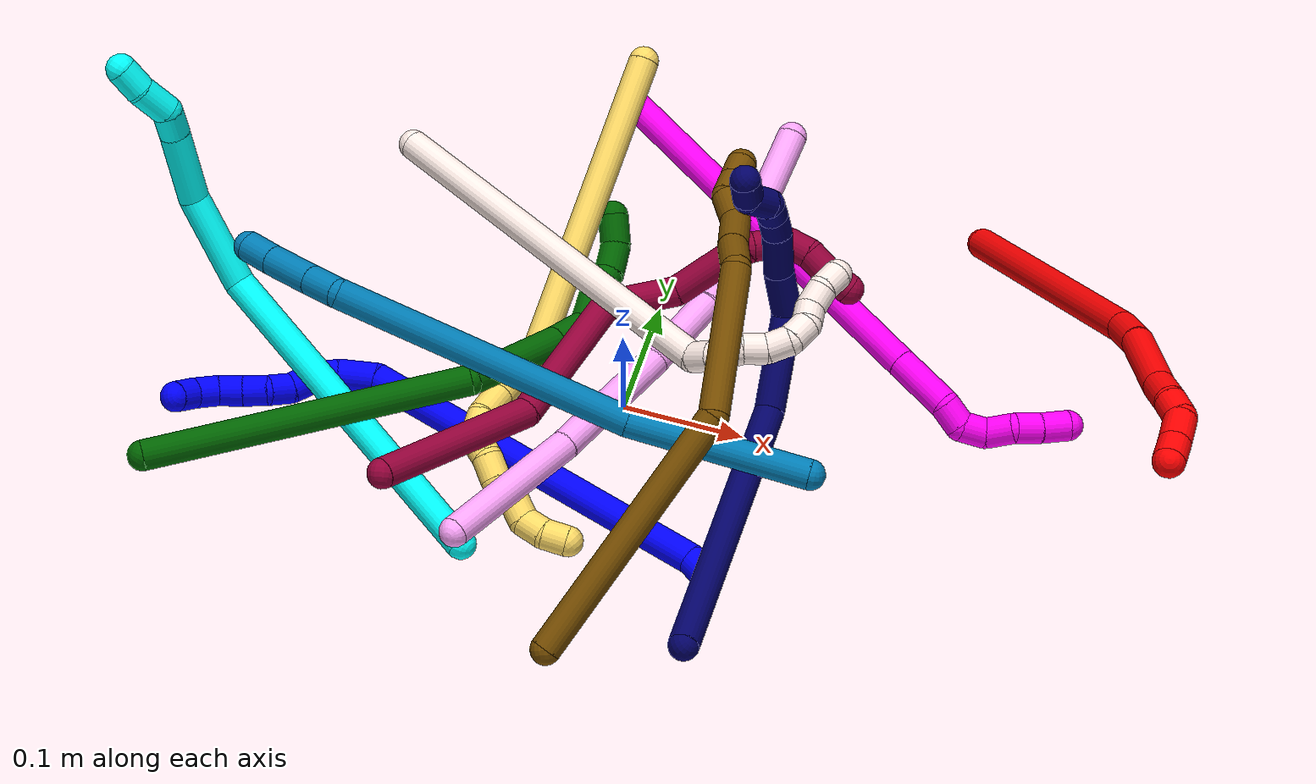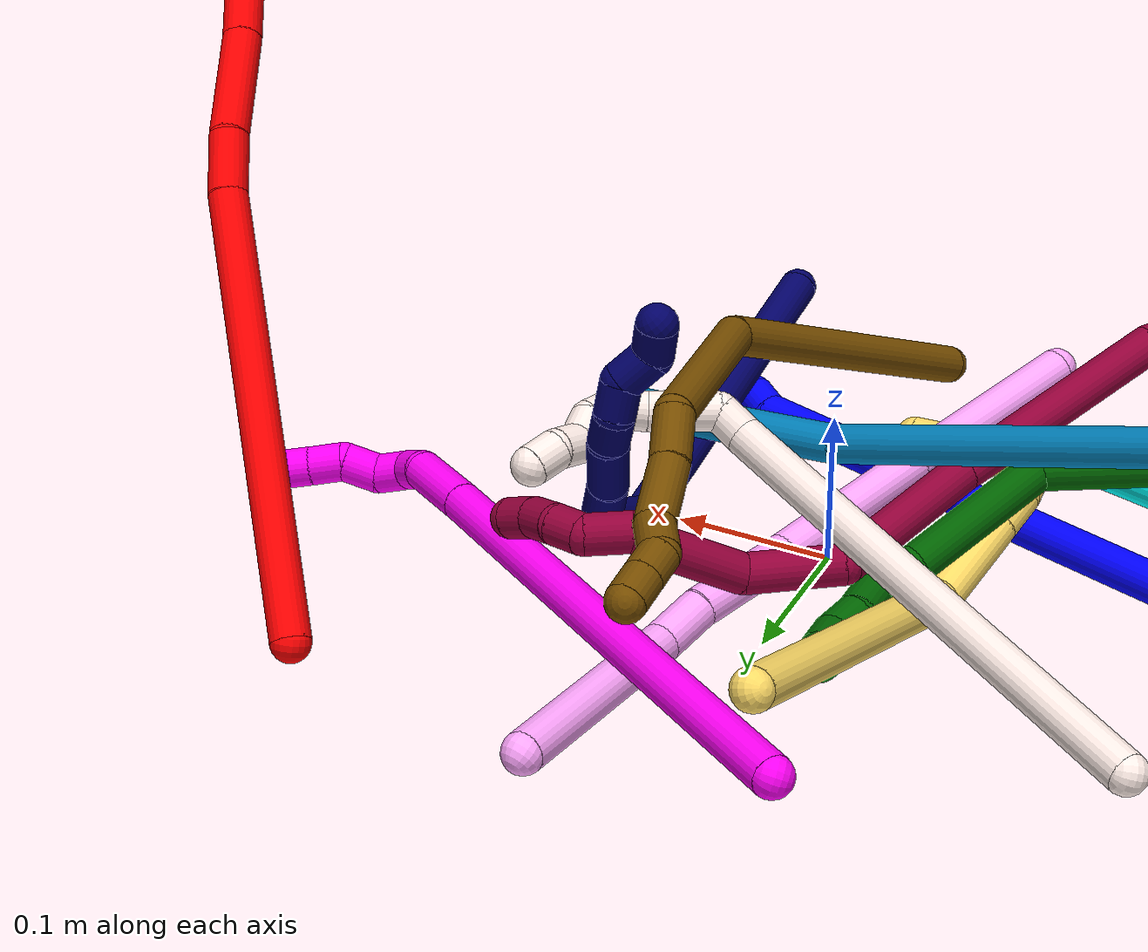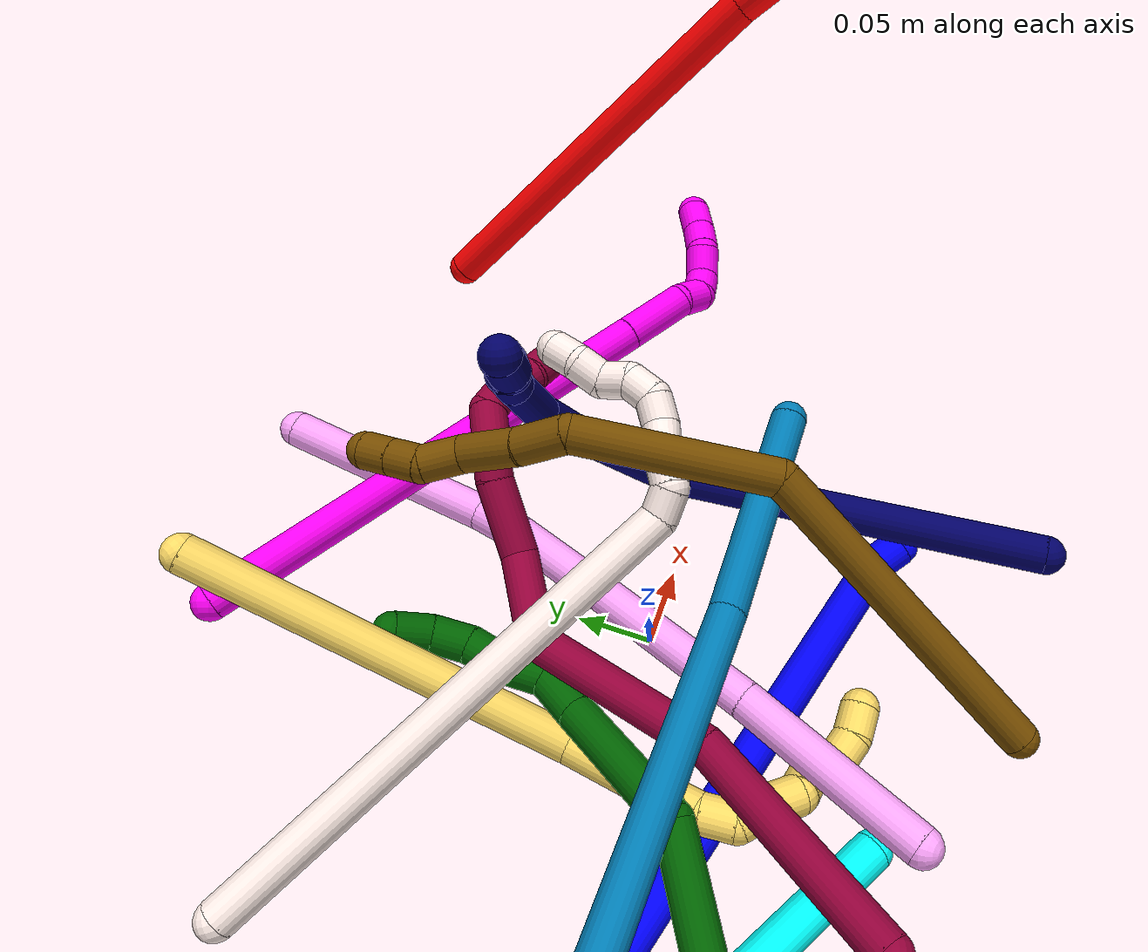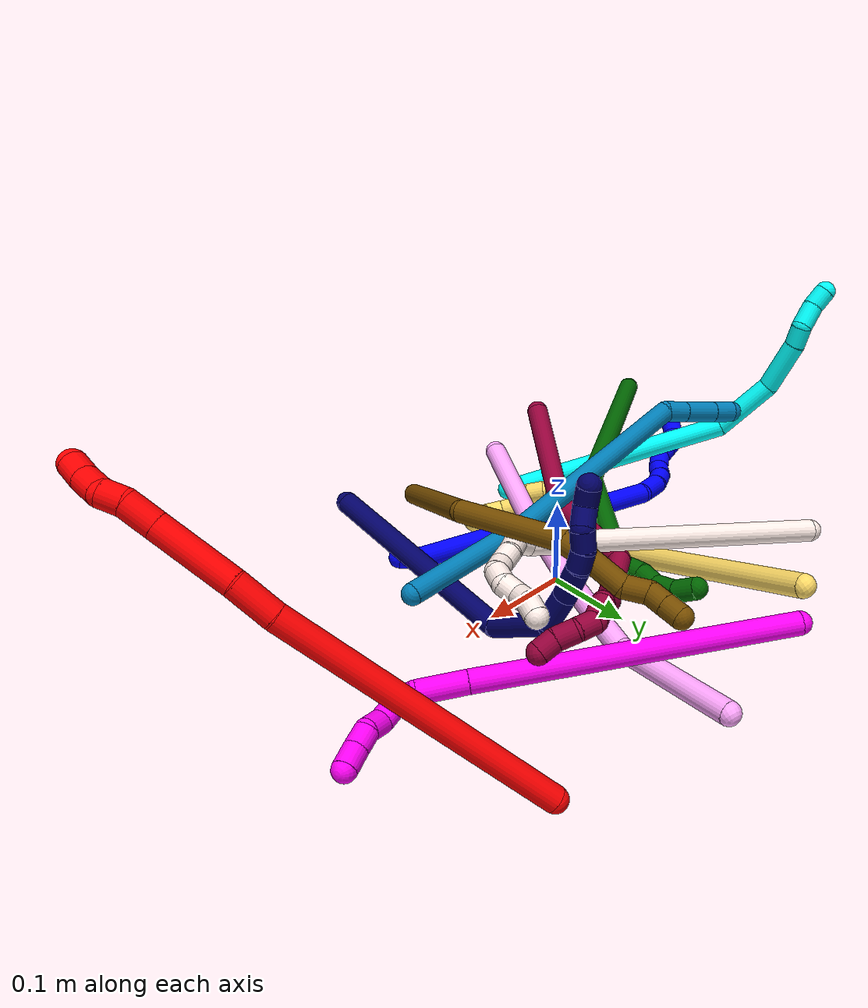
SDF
<sdf version="1.7">
 <world name="default">
  <plugin name="TubeGeneratorPlugin" filename="libtube_generator_plugin.so"/>
  <model name="photoneo_s_sensor">
   <static>1</static>
   <pose>0 0 2 1.57079 1.57079 3.14159</pose>
   <link name="link">
    <inertial><mass>0.1</mass></inertial>
    <sensor name="sensor" type="depth">
     <update_rate>30</update_rate>
     <camera>
      <horizontal_fov>1.22</horizontal_fov>
      <image><width>1920</width><height>1200</height><format>B8G8R8</format></image>
      <clip><near>0.1</near><far>4</far></clip>
      <depth_camera><output>points</output></depth_camera>
     </camera>
     <plugin name="camera_plugin" filename="libgazebo_ros_depth_camera.so">
      <baseline>0.2</baseline>
      <alwaysOn>1</alwaysOn>
      <updateRate>0.0</updateRate>
      <cameraName>camera_ir</cameraName>
      <imageTopicName>/camera/color/image_raw</imageTopicName>
      <cameraInfoTopicName>/camera/color/camera_info</cameraInfoTopicName>
      <depthImageTopicName>/camera/depth/image_raw</depthImageTopicName>
      <depthImageCameraInfoTopicName>/camera/depth/camera_info</depthImageCameraInfoTopicName>
      <pointCloudTopicName>/camera/depth/points</pointCloudTopicName>
      <frameName>fr_optical</frameName>
      <pointCloudCutoff>0.1</pointCloudCutoff>
      <pointCloudCutoffMax>2.0</pointCloudCutoffMax>
      <distortionK1>0</distortionK1>
      <distortionK2>0</distortionK2>
      <distortionK3>0</distortionK3>
      <distortionT1>0</distortionT1>
      <distortionT2>0</distortionT2>
      <CxPrime>0</CxPrime>
      <Cx>0</Cx>
      <Cy>0</Cy>
      <focalLength>0</focalLength>
      <hackBaseline>0</hackBaseline>
     </plugin>
    </sensor>
   </link>
  </model>
  <gravity>0 0 -9.8</gravity>
  <magnetic_field>6e-06 2.3e-05 -4.2e-05</magnetic_field>
  <atmosphere type="adiabatic"/>
  <physics name="default_physics" default="0" type="ode">
   <max_step_size>0.003</max_step_size>
   <real_time_factor>1</real_time_factor>
   <real_time_update_rate>1000</real_time_update_rate>
   <max_contacts>10000</max_contacts>
   <ode>
    <solver>
     <type>quick</type>
     <iters>100</iters>
     <sor>1.3</sor>
     <use_dynamic_moi_rescaling>0</use_dynamic_moi_rescaling>
    </solver>
    <constraints>
     <contact_max_correcting_vel>0</contact_max_correcting_vel>
     <contact_surface_layer>0.001</contact_surface_layer>
     <cfm>0</cfm>
     <erp>0.2</erp>
    </constraints>
   </ode>
  </physics>
  <scene><ambient>0.4 0.4 0.4 1</ambient><background>0.7 0.7 0.7 1</background><shadows>0</shadows></scene>
  <audio><device>default</device></audio>
  <spherical_coordinates>
   <surface_model>EARTH_WGS84</surface_model>
   <latitude_deg>0</latitude_deg>
   <longitude_deg>0</longitude_deg>
   <elevation>0</elevation>
   <heading_deg>0</heading_deg>
  </spherical_coordinates>
  <model name="bin">
   <static>1</static>
   <link name="bottom">
    <collision name="collision-bottom">
     <pose>0 0 -0.01 0 -0 0</pose>
     <geometry><box><size>0.8 0.6 0.02</size></box></geometry>
     <surface>
      <friction><ode><mu>100</mu><mu2>100</mu2></ode></friction>
      <contact><collide_bitmask>65535</collide_bitmask></contact>
     </surface>
    </collision>
   </link>
   <link name="west_wall">
    <collision name="collision-west_wall">
     <pose>-0.41 0 0.1 0 -0 0</pose>
     <geometry><box><size>0.02 0.6 0.2</size></box></geometry>
     <surface>
      <friction><ode><mu>100</mu><mu2>100</mu2></ode></friction>
      <contact><collide_bitmask>65535</collide_bitmask></contact>
     </surface>
    </collision>
   </link>
   <link name="east_wall">
    <collision name="collision-east_wall">
     <pose>0.41 0 0.1 0 -0 0</pose>
     <geometry><box><size>0.02 0.6 0.2</size></box></geometry>
     <surface>
      <friction><ode><mu>100</mu><mu2>100</mu2></ode></friction>
      <contact><collide_bitmask>65535</collide_bitmask></contact>
     </surface>
    </collision>
   </link>
   <link name="south_wall">
    <collision name="collision-south_wall">
     <pose>0 -0.31 0.1 0 -0 0</pose>
     <geometry><box><size>0.8 0.02 0.2</size></box></geometry>
     <surface>
      <friction><ode><mu>100</mu><mu2>100</mu2></ode></friction>
      <contact><collide_bitmask>65535</collide_bitmask></contact>
     </surface>
    </collision>
   </link>
   <link name="north_wall">
    <collision name="collision-north_wall">
     <pose>0 0.31 0.1 0 -0 0</pose>
     <geometry><box><size>0.8 0.02 0.2</size></box></geometry>
     <surface>
      <friction><ode><mu>100</mu><mu2>100</mu2></ode></friction>
      <contact><collide_bitmask>65535</collide_bitmask></contact>
     </surface>
    </collision>
   </link>
  </model>
  <model name="1">
   <static>0</static>
   <link name="1">
    <collision name="collision-cylinder-e_1_1_4">
     <pose>-0.007638 -0.00194 0.007285 0.260299 -0.791988 -0.109335</pose>
     <geometry><cylinder><radius>0.0125</radius><length>0.021464</length></cylinder></geometry>
     <surface>
      <friction><ode><mu>1.16</mu><mu2>1.16</mu2><slip1>0</slip1><slip2>0</slip2></ode></friction>
      <contact><ode><kp>1e+06</kp><kd>1</kd><max_vel>0</max_vel><min_depth>0.001</min_depth></ode></contact>
     </surface>
    </collision>
    <visual name="visual-cylinder-e_1_1_4">
     <pose>-0.007638 -0.00194 0.007285 0.260299 -0.791988 -0.109335</pose>
     <geometry><cylinder><radius>0.0125</radius><length>0.021464</length></cylinder></geometry>
     <material><ambient>0 0 1 1</ambient></material>
    </visual>
    <collision name="collision-cylinder-e_2_4_5">
     <pose>-0.13406 0.026539 0.105527 -0.322742 -0.891536 0.155261</pose>
     <geometry><cylinder><radius>0.0125</radius><length>0.305341</length></cylinder></geometry>
     <surface>
      <friction><ode><mu>1.16</mu><mu2>1.16</mu2><slip1>0</slip1><slip2>0</slip2></ode></friction>
      <contact><ode><kp>1e+06</kp><kd>1</kd><max_vel>0</max_vel><min_depth>0.001</min_depth></ode></contact>
     </surface>
    </collision>
    <visual name="visual-cylinder-e_2_4_5">
     <pose>-0.13406 0.026539 0.105527 -0.322742 -0.891536 0.155261</pose>
     <geometry><cylinder><radius>0.0125</radius><length>0.305341</length></cylinder></geometry>
     <material><ambient>0 0 1 1</ambient></material>
    </visual>
    <collision name="collision-cylinder-e_3_5_6">
     <pose>-0.261955 0.066151 0.205762 -0.780838 -0.609185 0.25733</pose>
     <geometry><cylinder><radius>0.0125</radius><length>0.031847</length></cylinder></geometry>
     <surface>
      <friction><ode><mu>1.16</mu><mu2>1.16</mu2><slip1>0</slip1><slip2>0</slip2></ode></friction>
      <contact><ode><kp>1e+06</kp><kd>1</kd><max_vel>0</max_vel><min_depth>0.001</min_depth></ode></contact>
     </surface>
    </collision>
    <visual name="visual-cylinder-e_3_5_6">
     <pose>-0.261955 0.066151 0.205762 -0.780838 -0.609185 0.25733</pose>
     <geometry><cylinder><radius>0.0125</radius><length>0.031847</length></cylinder></geometry>
     <material><ambient>0 0 1 1</ambient></material>
    </visual>
    <collision name="collision-cylinder-e_4_6_7">
     <pose>-0.275228 0.083756 0.219268 -1.10495 -0.416077 0.258829</pose>
     <geometry><cylinder><radius>0.0125</radius><length>0.02059</length></cylinder></geometry>
     <surface>
      <friction><ode><mu>1.16</mu><mu2>1.16</mu2><slip1>0</slip1><slip2>0</slip2></ode></friction>
      <contact><ode><kp>1e+06</kp><kd>1</kd><max_vel>0</max_vel><min_depth>0.001</min_depth></ode></contact>
     </surface>
    </collision>
    <visual name="visual-cylinder-e_4_6_7">
     <pose>-0.275228 0.083756 0.219268 -1.10495 -0.416077 0.258829</pose>
     <geometry><cylinder><radius>0.0125</radius><length>0.02059</length></cylinder></geometry>
     <material><ambient>0 0 1 1</ambient></material>
    </visual>
    <collision name="collision-cylinder-e_5_7_8">
     <pose>-0.280672 0.102002 0.226082 -1.31383 -0.125615 0.096923</pose>
     <geometry><cylinder><radius>0.0125</radius><length>0.020495</length></cylinder></geometry>
     <surface>
      <friction><ode><mu>1.16</mu><mu2>1.16</mu2><slip1>0</slip1><slip2>0</slip2></ode></friction>
      <contact><ode><kp>1e+06</kp><kd>1</kd><max_vel>0</max_vel><min_depth>0.001</min_depth></ode></contact>
     </surface>
    </collision>
    <visual name="visual-cylinder-e_5_7_8">
     <pose>-0.280672 0.102002 0.226082 -1.31383 -0.125615 0.096923</pose>
     <geometry><cylinder><radius>0.0125</radius><length>0.020495</length></cylinder></geometry>
     <material><ambient>0 0 1 1</ambient></material>
    </visual>
    <collision name="collision-cylinder-e_6_8_9">
     <pose>-0.286473 0.120682 0.229949 -1.42674 -0.467836 0.406719</pose>
     <geometry><cylinder><radius>0.0125</radius><length>0.020031</length></cylinder></geometry>
     <surface>
      <friction><ode><mu>1.16</mu><mu2>1.16</mu2><slip1>0</slip1><slip2>0</slip2></ode></friction>
      <contact><ode><kp>1e+06</kp><kd>1</kd><max_vel>0</max_vel><min_depth>0.001</min_depth></ode></contact>
     </surface>
    </collision>
    <visual name="visual-cylinder-e_6_8_9">
     <pose>-0.286473 0.120682 0.229949 -1.42674 -0.467836 0.406719</pose>
     <geometry><cylinder><radius>0.0125</radius><length>0.020031</length></cylinder></geometry>
     <material><ambient>0 0 1 1</ambient></material>
    </visual>
    <collision name="collision-cylinder-e_7_9_10">
     <pose>-0.29587 0.13672 0.236197 -0.966505 -0.509369 0.271545</pose>
     <geometry><cylinder><radius>0.0125</radius><length>0.02002</length></cylinder></geometry>
     <surface>
      <friction><ode><mu>1.16</mu><mu2>1.16</mu2><slip1>0</slip1><slip2>0</slip2></ode></friction>
      <contact><ode><kp>1e+06</kp><kd>1</kd><max_vel>0</max_vel><min_depth>0.001</min_depth></ode></contact>
     </surface>
    </collision>
    <visual name="visual-cylinder-e_7_9_10">
     <pose>-0.29587 0.13672 0.236197 -0.966505 -0.509369 0.271545</pose>
     <geometry><cylinder><radius>0.0125</radius><length>0.02002</length></cylinder></geometry>
     <material><ambient>0 0 1 1</ambient></material>
    </visual>
    <collision name="collision-cylinder-e_8_10_11">
     <pose>-0.306077 0.151041 0.245726 -1.00143 -0.561567 0.313065</pose>
     <geometry><cylinder><radius>0.0125</radius><length>0.020002</length></cylinder></geometry>
     <surface>
      <friction><ode><mu>1.16</mu><mu2>1.16</mu2><slip1>0</slip1><slip2>0</slip2></ode></friction>
      <contact><ode><kp>1e+06</kp><kd>1</kd><max_vel>0</max_vel><min_depth>0.001</min_depth></ode></contact>
     </surface>
    </collision>
    <visual name="visual-cylinder-e_8_10_11">
     <pose>-0.306077 0.151041 0.245726 -1.00143 -0.561567 0.313065</pose>
     <geometry><cylinder><radius>0.0125</radius><length>0.020002</length></cylinder></geometry>
     <material><ambient>0 0 1 1</ambient></material>
    </visual>
    <collision name="collision-cylinder-e_9_11_12">
     <pose>-0.315821 0.166876 0.252554 -1.31637 -0.456584 0.355501</pose>
     <geometry><cylinder><radius>0.0125</radius><length>0.020044</length></cylinder></geometry>
     <surface>
      <friction><ode><mu>1.16</mu><mu2>1.16</mu2><slip1>0</slip1><slip2>0</slip2></ode></friction>
      <contact><ode><kp>1e+06</kp><kd>1</kd><max_vel>0</max_vel><min_depth>0.001</min_depth></ode></contact>
     </surface>
    </collision>
    <visual name="visual-cylinder-e_9_11_12">
     <pose>-0.315821 0.166876 0.252554 -1.31637 -0.456584 0.355501</pose>
     <geometry><cylinder><radius>0.0125</radius><length>0.020044</length></cylinder></geometry>
     <material><ambient>0 0 1 1</ambient></material>
    </visual>
    <collision name="collision-cylinder-e_10_12_2">
     <pose>-0.323505 0.184671 0.251918 -1.87963 -0.329742 0.447817</pose>
     <geometry><cylinder><radius>0.0125</radius><length>0.020167</length></cylinder></geometry>
     <surface>
      <friction><ode><mu>1.16</mu><mu2>1.16</mu2><slip1>0</slip1><slip2>0</slip2></ode></friction>
      <contact><ode><kp>1e+06</kp><kd>1</kd><max_vel>0</max_vel><min_depth>0.001</min_depth></ode></contact>
     </surface>
    </collision>
    <visual name="visual-cylinder-e_10_12_2">
     <pose>-0.323505 0.184671 0.251918 -1.87963 -0.329742 0.447817</pose>
     <geometry><cylinder><radius>0.0125</radius><length>0.020167</length></cylinder></geometry>
     <material><ambient>0 0 1 1</ambient></material>
    </visual>
    <collision name="collision-sphere-2">
     <pose>-0.32677 0.19376 0.249018 0 -0 0</pose>
     <geometry><sphere><radius>0.0125</radius></sphere></geometry>
     <surface>
      <friction><ode><mu>1.16</mu><mu2>1.16</mu2><slip1>0</slip1><slip2>0</slip2></ode></friction>
      <contact><ode><kp>1e+06</kp><kd>1</kd><max_vel>0</max_vel><min_depth>0.001</min_depth></ode></contact>
     </surface>
    </collision>
    <visual name="visual-sphere-2">
     <pose>-0.32677 0.19376 0.249018 0 -0 0</pose>
     <geometry><sphere><radius>0.0125</radius></sphere></geometry>
     <material><ambient>0 0 1 1</ambient></material>
    </visual>
    <collision name="collision-sphere-12">
     <pose>-0.32024 0.175582 0.254818 0 -0 0</pose>
     <geometry><sphere><radius>0.0125</radius></sphere></geometry>
     <surface>
      <friction><ode><mu>1.16</mu><mu2>1.16</mu2><slip1>0</slip1><slip2>0</slip2></ode></friction>
      <contact><ode><kp>1e+06</kp><kd>1</kd><max_vel>0</max_vel><min_depth>0.001</min_depth></ode></contact>
     </surface>
    </collision>
    <visual name="visual-sphere-12">
     <pose>-0.32024 0.175582 0.254818 0 -0 0</pose>
     <geometry><sphere><radius>0.0125</radius></sphere></geometry>
     <material><ambient>0 0 1 1</ambient></material>
    </visual>
    <collision name="collision-sphere-11">
     <pose>-0.311403 0.15817 0.25029 0 -0 0</pose>
     <geometry><sphere><radius>0.0125</radius></sphere></geometry>
     <surface>
      <friction><ode><mu>1.16</mu><mu2>1.16</mu2><slip1>0</slip1><slip2>0</slip2></ode></friction>
      <contact><ode><kp>1e+06</kp><kd>1</kd><max_vel>0</max_vel><min_depth>0.001</min_depth></ode></contact>
     </surface>
    </collision>
    <visual name="visual-sphere-11">
     <pose>-0.311403 0.15817 0.25029 0 -0 0</pose>
     <geometry><sphere><radius>0.0125</radius></sphere></geometry>
     <material><ambient>0 0 1 1</ambient></material>
    </visual>
    <collision name="collision-sphere-10">
     <pose>-0.300752 0.143911 0.241163 0 -0 0</pose>
     <geometry><sphere><radius>0.0125</radius></sphere></geometry>
     <surface>
      <friction><ode><mu>1.16</mu><mu2>1.16</mu2><slip1>0</slip1><slip2>0</slip2></ode></friction>
      <contact><ode><kp>1e+06</kp><kd>1</kd><max_vel>0</max_vel><min_depth>0.001</min_depth></ode></contact>
     </surface>
    </collision>
    <visual name="visual-sphere-10">
     <pose>-0.300752 0.143911 0.241163 0 -0 0</pose>
     <geometry><sphere><radius>0.0125</radius></sphere></geometry>
     <material><ambient>0 0 1 1</ambient></material>
    </visual>
    <collision name="collision-sphere-9">
     <pose>-0.290989 0.129528 0.231232 0 -0 0</pose>
     <geometry><sphere><radius>0.0125</radius></sphere></geometry>
     <surface>
      <friction><ode><mu>1.16</mu><mu2>1.16</mu2><slip1>0</slip1><slip2>0</slip2></ode></friction>
      <contact><ode><kp>1e+06</kp><kd>1</kd><max_vel>0</max_vel><min_depth>0.001</min_depth></ode></contact>
     </surface>
    </collision>
    <visual name="visual-sphere-9">
     <pose>-0.290989 0.129528 0.231232 0 -0 0</pose>
     <geometry><sphere><radius>0.0125</radius></sphere></geometry>
     <material><ambient>0 0 1 1</ambient></material>
    </visual>
    <collision name="collision-sphere-4">
     <pose>-0.015277 -0.00388 0.014569 0 -0 0</pose>
     <geometry><sphere><radius>0.0125</radius></sphere></geometry>
     <surface>
      <friction><ode><mu>1.16</mu><mu2>1.16</mu2><slip1>0</slip1><slip2>0</slip2></ode></friction>
      <contact><ode><kp>1e+06</kp><kd>1</kd><max_vel>0</max_vel><min_depth>0.001</min_depth></ode></contact>
     </surface>
    </collision>
    <visual name="visual-sphere-4">
     <pose>-0.015277 -0.00388 0.014569 0 -0 0</pose>
     <geometry><sphere><radius>0.0125</radius></sphere></geometry>
     <material><ambient>0 0 1 1</ambient></material>
    </visual>
    <collision name="collision-sphere-1">
     <geometry><sphere><radius>0.0125</radius></sphere></geometry>
     <surface>
      <friction><ode><mu>1.16</mu><mu2>1.16</mu2><slip1>0</slip1><slip2>0</slip2></ode></friction>
      <contact><ode><kp>1e+06</kp><kd>1</kd><max_vel>0</max_vel><min_depth>0.001</min_depth></ode></contact>
     </surface>
    </collision>
    <visual name="visual-sphere-1">
     <geometry><sphere><radius>0.0125</radius></sphere></geometry>
     <material><ambient>0 0 1 1</ambient></material>
    </visual>
    <collision name="collision-sphere-8">
     <pose>-0.281956 0.111835 0.228665 0 -0 0</pose>
     <geometry><sphere><radius>0.0125</radius></sphere></geometry>
     <surface>
      <friction><ode><mu>1.16</mu><mu2>1.16</mu2><slip1>0</slip1><slip2>0</slip2></ode></friction>
      <contact><ode><kp>1e+06</kp><kd>1</kd><max_vel>0</max_vel><min_depth>0.001</min_depth></ode></contact>
     </surface>
    </collision>
    <visual name="visual-sphere-8">
     <pose>-0.281956 0.111835 0.228665 0 -0 0</pose>
     <geometry><sphere><radius>0.0125</radius></sphere></geometry>
     <material><ambient>0 0 1 1</ambient></material>
    </visual>
    <collision name="collision-sphere-5">
     <pose>-0.252844 0.056959 0.196486 0 -0 0</pose>
     <geometry><sphere><radius>0.0125</radius></sphere></geometry>
     <surface>
      <friction><ode><mu>1.16</mu><mu2>1.16</mu2><slip1>0</slip1><slip2>0</slip2></ode></friction>
      <contact><ode><kp>1e+06</kp><kd>1</kd><max_vel>0</max_vel><min_depth>0.001</min_depth></ode></contact>
     </surface>
    </collision>
    <visual name="visual-sphere-5">
     <pose>-0.252844 0.056959 0.196486 0 -0 0</pose>
     <geometry><sphere><radius>0.0125</radius></sphere></geometry>
     <material><ambient>0 0 1 1</ambient></material>
    </visual>
    <collision name="collision-sphere-6">
     <pose>-0.271067 0.075343 0.215038 0 -0 0</pose>
     <geometry><sphere><radius>0.0125</radius></sphere></geometry>
     <surface>
      <friction><ode><mu>1.16</mu><mu2>1.16</mu2><slip1>0</slip1><slip2>0</slip2></ode></friction>
      <contact><ode><kp>1e+06</kp><kd>1</kd><max_vel>0</max_vel><min_depth>0.001</min_depth></ode></contact>
     </surface>
    </collision>
    <visual name="visual-sphere-6">
     <pose>-0.271067 0.075343 0.215038 0 -0 0</pose>
     <geometry><sphere><radius>0.0125</radius></sphere></geometry>
     <material><ambient>0 0 1 1</ambient></material>
    </visual>
    <collision name="collision-sphere-7">
     <pose>-0.279389 0.092169 0.223498 0 -0 0</pose>
     <geometry><sphere><radius>0.0125</radius></sphere></geometry>
     <surface>
      <friction><ode><mu>1.16</mu><mu2>1.16</mu2><slip1>0</slip1><slip2>0</slip2></ode></friction>
      <contact><ode><kp>1e+06</kp><kd>1</kd><max_vel>0</max_vel><min_depth>0.001</min_depth></ode></contact>
     </surface>
    </collision>
    <visual name="visual-sphere-7">
     <pose>-0.279389 0.092169 0.223498 0 -0 0</pose>
     <geometry><sphere><radius>0.0125</radius></sphere></geometry>
     <material><ambient>0 0 1 1</ambient></material>
    </visual>
    <inertial>
     <pose>-0.182996 0.058457 0.144943 0 -0 0</pose>
     <mass>0.5</mass>
     <inertia>
      <ixx>0.001703</ixx>
      <ixy>0</ixy>
      <ixz>0</ixz>
      <iyy>0.002584</iyy>
      <iyz>0</iyz>
      <izz>0.001396</izz>
     </inertia>
    </inertial>
   </link>
   <pose>0.112448 -0.141437 0.01465 2.97616 0.628535 -0.589363</pose>
  </model>
  <model name="2">
   <static>0</static>
   <link name="2">
    <collision name="collision-cylinder-e_1_1_4">
     <pose>0.062028 -0.040811 0.123555 0.319023 0.444832 0.072735</pose>
     <geometry><cylinder><radius>0.0125</radius><length>0.288296</length></cylinder></geometry>
     <surface>
      <friction><ode><mu>1.16</mu><mu2>1.16</mu2><slip1>0</slip1><slip2>0</slip2></ode></friction>
      <contact><ode><kp>1e+06</kp><kd>1</kd><max_vel>0</max_vel><min_depth>0.001</min_depth></ode></contact>
     </surface>
    </collision>
    <visual name="visual-cylinder-e_1_1_4">
     <pose>0.062028 -0.040811 0.123555 0.319023 0.444832 0.072735</pose>
     <geometry><cylinder><radius>0.0125</radius><length>0.288296</length></cylinder></geometry>
     <material><ambient>1 0 0 1</ambient></material>
    </visual>
    <collision name="collision-cylinder-e_2_4_5">
     <pose>0.130399 -0.088785 0.265115 0.378667 0.316359 0.061115</pose>
     <geometry><cylinder><radius>0.0125</radius><length>0.040781</length></cylinder></geometry>
     <surface>
      <friction><ode><mu>1.16</mu><mu2>1.16</mu2><slip1>0</slip1><slip2>0</slip2></ode></friction>
      <contact><ode><kp>1e+06</kp><kd>1</kd><max_vel>0</max_vel><min_depth>0.001</min_depth></ode></contact>
     </surface>
    </collision>
    <visual name="visual-cylinder-e_2_4_5">
     <pose>0.130399 -0.088785 0.265115 0.378667 0.316359 0.061115</pose>
     <geometry><cylinder><radius>0.0125</radius><length>0.040781</length></cylinder></geometry>
     <material><ambient>1 0 0 1</ambient></material>
    </visual>
    <collision name="collision-cylinder-e_3_5_6">
     <pose>0.147585 -0.11514 0.313843 0.558342 0.29083 0.083912</pose>
     <geometry><cylinder><radius>0.0125</radius><length>0.075623</length></cylinder></geometry>
     <surface>
      <friction><ode><mu>1.16</mu><mu2>1.16</mu2><slip1>0</slip1><slip2>0</slip2></ode></friction>
      <contact><ode><kp>1e+06</kp><kd>1</kd><max_vel>0</max_vel><min_depth>0.001</min_depth></ode></contact>
     </surface>
    </collision>
    <visual name="visual-cylinder-e_3_5_6">
     <pose>0.147585 -0.11514 0.313843 0.558342 0.29083 0.083912</pose>
     <geometry><cylinder><radius>0.0125</radius><length>0.075623</length></cylinder></geometry>
     <material><ambient>1 0 0 1</ambient></material>
    </visual>
    <collision name="collision-cylinder-e_4_6_7">
     <pose>0.163206 -0.140733 0.357169 0.470003 0.325964 0.078702</pose>
     <geometry><cylinder><radius>0.0125</radius><length>0.029845</length></cylinder></geometry>
     <surface>
      <friction><ode><mu>1.16</mu><mu2>1.16</mu2><slip1>0</slip1><slip2>0</slip2></ode></friction>
      <contact><ode><kp>1e+06</kp><kd>1</kd><max_vel>0</max_vel><min_depth>0.001</min_depth></ode></contact>
     </surface>
    </collision>
    <visual name="visual-cylinder-e_4_6_7">
     <pose>0.163206 -0.140733 0.357169 0.470003 0.325964 0.078702</pose>
     <geometry><cylinder><radius>0.0125</radius><length>0.029845</length></cylinder></geometry>
     <material><ambient>1 0 0 1</ambient></material>
    </visual>
    <collision name="collision-cylinder-e_5_7_8">
     <pose>0.172844 -0.153178 0.376415 0.738287 0.495998 0.195301</pose>
     <geometry><cylinder><radius>0.0125</radius><length>0.020419</length></cylinder></geometry>
     <surface>
      <friction><ode><mu>1.16</mu><mu2>1.16</mu2><slip1>0</slip1><slip2>0</slip2></ode></friction>
      <contact><ode><kp>1e+06</kp><kd>1</kd><max_vel>0</max_vel><min_depth>0.001</min_depth></ode></contact>
     </surface>
    </collision>
    <visual name="visual-cylinder-e_5_7_8">
     <pose>0.172844 -0.153178 0.376415 0.738287 0.495998 0.195301</pose>
     <geometry><cylinder><radius>0.0125</radius><length>0.020419</length></cylinder></geometry>
     <material><ambient>1 0 0 1</ambient></material>
    </visual>
    <collision name="collision-cylinder-e_6_8_9">
     <pose>0.177481 -0.169571 0.38925 1.03153 -0.018317 -0.010385</pose>
     <geometry><cylinder><radius>0.0125</radius><length>0.024127</length></cylinder></geometry>
     <surface>
      <friction><ode><mu>1.16</mu><mu2>1.16</mu2><slip1>0</slip1><slip2>0</slip2></ode></friction>
      <contact><ode><kp>1e+06</kp><kd>1</kd><max_vel>0</max_vel><min_depth>0.001</min_depth></ode></contact>
     </surface>
    </collision>
    <visual name="visual-cylinder-e_6_8_9">
     <pose>0.177481 -0.169571 0.38925 1.03153 -0.018317 -0.010385</pose>
     <geometry><cylinder><radius>0.0125</radius><length>0.024127</length></cylinder></geometry>
     <material><ambient>1 0 0 1</ambient></material>
    </visual>
    <collision name="collision-cylinder-e_7_9_2">
     <pose>0.176605 -0.187909 0.402156 0.871936 -0.062768 -0.029249</pose>
     <geometry><cylinder><radius>0.0125</radius><length>0.020909</length></cylinder></geometry>
     <surface>
      <friction><ode><mu>1.16</mu><mu2>1.16</mu2><slip1>0</slip1><slip2>0</slip2></ode></friction>
      <contact><ode><kp>1e+06</kp><kd>1</kd><max_vel>0</max_vel><min_depth>0.001</min_depth></ode></contact>
     </surface>
    </collision>
    <visual name="visual-cylinder-e_7_9_2">
     <pose>0.176605 -0.187909 0.402156 0.871936 -0.062768 -0.029249</pose>
     <geometry><cylinder><radius>0.0125</radius><length>0.020909</length></cylinder></geometry>
     <material><ambient>1 0 0 1</ambient></material>
    </visual>
    <collision name="collision-sphere-2">
     <pose>0.175949 -0.195897 0.408868 0 -0 0</pose>
     <geometry><sphere><radius>0.0125</radius></sphere></geometry>
     <surface>
      <friction><ode><mu>1.16</mu><mu2>1.16</mu2><slip1>0</slip1><slip2>0</slip2></ode></friction>
      <contact><ode><kp>1e+06</kp><kd>1</kd><max_vel>0</max_vel><min_depth>0.001</min_depth></ode></contact>
     </surface>
    </collision>
    <visual name="visual-sphere-2">
     <pose>0.175949 -0.195897 0.408868 0 -0 0</pose>
     <geometry><sphere><radius>0.0125</radius></sphere></geometry>
     <material><ambient>1 0 0 1</ambient></material>
    </visual>
    <collision name="collision-sphere-9">
     <pose>0.177261 -0.179921 0.395443 0 -0 0</pose>
     <geometry><sphere><radius>0.0125</radius></sphere></geometry>
     <surface>
      <friction><ode><mu>1.16</mu><mu2>1.16</mu2><slip1>0</slip1><slip2>0</slip2></ode></friction>
      <contact><ode><kp>1e+06</kp><kd>1</kd><max_vel>0</max_vel><min_depth>0.001</min_depth></ode></contact>
     </surface>
    </collision>
    <visual name="visual-sphere-9">
     <pose>0.177261 -0.179921 0.395443 0 -0 0</pose>
     <geometry><sphere><radius>0.0125</radius></sphere></geometry>
     <material><ambient>1 0 0 1</ambient></material>
    </visual>
    <collision name="collision-sphere-4">
     <pose>0.124056 -0.081621 0.247109 0 -0 0</pose>
     <geometry><sphere><radius>0.0125</radius></sphere></geometry>
     <surface>
      <friction><ode><mu>1.16</mu><mu2>1.16</mu2><slip1>0</slip1><slip2>0</slip2></ode></friction>
      <contact><ode><kp>1e+06</kp><kd>1</kd><max_vel>0</max_vel><min_depth>0.001</min_depth></ode></contact>
     </surface>
    </collision>
    <visual name="visual-sphere-4">
     <pose>0.124056 -0.081621 0.247109 0 -0 0</pose>
     <geometry><sphere><radius>0.0125</radius></sphere></geometry>
     <material><ambient>1 0 0 1</ambient></material>
    </visual>
    <collision name="collision-sphere-1">
     <geometry><sphere><radius>0.0125</radius></sphere></geometry>
     <surface>
      <friction><ode><mu>1.16</mu><mu2>1.16</mu2><slip1>0</slip1><slip2>0</slip2></ode></friction>
      <contact><ode><kp>1e+06</kp><kd>1</kd><max_vel>0</max_vel><min_depth>0.001</min_depth></ode></contact>
     </surface>
    </collision>
    <visual name="visual-sphere-1">
     <geometry><sphere><radius>0.0125</radius></sphere></geometry>
     <material><ambient>1 0 0 1</ambient></material>
    </visual>
    <collision name="collision-sphere-8">
     <pose>0.177702 -0.159222 0.383056 0 -0 0</pose>
     <geometry><sphere><radius>0.0125</radius></sphere></geometry>
     <surface>
      <friction><ode><mu>1.16</mu><mu2>1.16</mu2><slip1>0</slip1><slip2>0</slip2></ode></friction>
      <contact><ode><kp>1e+06</kp><kd>1</kd><max_vel>0</max_vel><min_depth>0.001</min_depth></ode></contact>
     </surface>
    </collision>
    <visual name="visual-sphere-8">
     <pose>0.177702 -0.159222 0.383056 0 -0 0</pose>
     <geometry><sphere><radius>0.0125</radius></sphere></geometry>
     <material><ambient>1 0 0 1</ambient></material>
    </visual>
    <collision name="collision-sphere-5">
     <pose>0.136743 -0.095949 0.283121 0 -0 0</pose>
     <geometry><sphere><radius>0.0125</radius></sphere></geometry>
     <surface>
      <friction><ode><mu>1.16</mu><mu2>1.16</mu2><slip1>0</slip1><slip2>0</slip2></ode></friction>
      <contact><ode><kp>1e+06</kp><kd>1</kd><max_vel>0</max_vel><min_depth>0.001</min_depth></ode></contact>
     </surface>
    </collision>
    <visual name="visual-sphere-5">
     <pose>0.136743 -0.095949 0.283121 0 -0 0</pose>
     <geometry><sphere><radius>0.0125</radius></sphere></geometry>
     <material><ambient>1 0 0 1</ambient></material>
    </visual>
    <collision name="collision-sphere-6">
     <pose>0.158428 -0.13433 0.344566 0 -0 0</pose>
     <geometry><sphere><radius>0.0125</radius></sphere></geometry>
     <surface>
      <friction><ode><mu>1.16</mu><mu2>1.16</mu2><slip1>0</slip1><slip2>0</slip2></ode></friction>
      <contact><ode><kp>1e+06</kp><kd>1</kd><max_vel>0</max_vel><min_depth>0.001</min_depth></ode></contact>
     </surface>
    </collision>
    <visual name="visual-sphere-6">
     <pose>0.158428 -0.13433 0.344566 0 -0 0</pose>
     <geometry><sphere><radius>0.0125</radius></sphere></geometry>
     <material><ambient>1 0 0 1</ambient></material>
    </visual>
    <collision name="collision-sphere-7">
     <pose>0.167985 -0.147135 0.369773 0 -0 0</pose>
     <geometry><sphere><radius>0.0125</radius></sphere></geometry>
     <surface>
      <friction><ode><mu>1.16</mu><mu2>1.16</mu2><slip1>0</slip1><slip2>0</slip2></ode></friction>
      <contact><ode><kp>1e+06</kp><kd>1</kd><max_vel>0</max_vel><min_depth>0.001</min_depth></ode></contact>
     </surface>
    </collision>
    <visual name="visual-sphere-7">
     <pose>0.167985 -0.147135 0.369773 0 -0 0</pose>
     <geometry><sphere><radius>0.0125</radius></sphere></geometry>
     <material><ambient>1 0 0 1</ambient></material>
    </visual>
    <inertial>
     <pose>0.101472 -0.078883 0.212623 0 -0 0</pose>
     <mass>0.5</mass>
     <inertia>
      <ixx>0.00201</ixx>
      <ixy>0</ixy>
      <ixz>0</ixz>
      <iyy>0.002088</iyy>
      <iyz>0</iyz>
      <izz>-0.000251</izz>
     </inertia>
    </inertial>
   </link>
   <pose>0.23869 0.235308 0.011498 0.439195 0.061565 0.044672</pose>
  </model>
  <model name="3">
   <static>0</static>
   <link name="3">
    <collision name="collision-cylinder-e_1_1_4">
     <pose>-0.042562 0.01414 0.134928 -0.104414 -0.304003 0.016009</pose>
     <geometry><cylinder><radius>0.0125</radius><length>0.284373</length></cylinder></geometry>
     <surface>
      <friction><ode><mu>1.16</mu><mu2>1.16</mu2><slip1>0</slip1><slip2>0</slip2></ode></friction>
      <contact><ode><kp>1e+06</kp><kd>1</kd><max_vel>0</max_vel><min_depth>0.001</min_depth></ode></contact>
     </surface>
    </collision>
    <visual name="visual-cylinder-e_1_1_4">
     <pose>-0.042562 0.01414 0.134928 -0.104414 -0.304003 0.016009</pose>
     <geometry><cylinder><radius>0.0125</radius><length>0.284373</length></cylinder></geometry>
     <material><ambient>0.003922 1 0.996078 1</ambient></material>
    </visual>
    <collision name="collision-cylinder-e_2_4_5">
     <pose>-0.107369 0.046316 0.296555 -0.594123 -0.60422 0.190228</pose>
     <geometry><cylinder><radius>0.0125</radius><length>0.078307</length></cylinder></geometry>
     <surface>
      <friction><ode><mu>1.16</mu><mu2>1.16</mu2><slip1>0</slip1><slip2>0</slip2></ode></friction>
      <contact><ode><kp>1e+06</kp><kd>1</kd><max_vel>0</max_vel><min_depth>0.001</min_depth></ode></contact>
     </surface>
    </collision>
    <visual name="visual-cylinder-e_2_4_5">
     <pose>-0.107369 0.046316 0.296555 -0.594123 -0.60422 0.190228</pose>
     <geometry><cylinder><radius>0.0125</radius><length>0.078307</length></cylinder></geometry>
     <material><ambient>0.003922 1 0.996078 1</ambient></material>
    </visual>
    <collision name="collision-cylinder-e_3_5_6">
     <pose>-0.150773 0.084504 0.333492 -1.10075 -0.752487 0.475663</pose>
     <geometry><cylinder><radius>0.0125</radius><length>0.061923</length></cylinder></geometry>
     <surface>
      <friction><ode><mu>1.16</mu><mu2>1.16</mu2><slip1>0</slip1><slip2>0</slip2></ode></friction>
      <contact><ode><kp>1e+06</kp><kd>1</kd><max_vel>0</max_vel><min_depth>0.001</min_depth></ode></contact>
     </surface>
    </collision>
    <visual name="visual-cylinder-e_3_5_6">
     <pose>-0.150773 0.084504 0.333492 -1.10075 -0.752487 0.475663</pose>
     <geometry><cylinder><radius>0.0125</radius><length>0.061923</length></cylinder></geometry>
     <material><ambient>0.003922 1 0.996078 1</ambient></material>
    </visual>
    <collision name="collision-cylinder-e_4_6_7">
     <pose>-0.179329 0.113946 0.346058 -1.32514 -0.657391 0.52017</pose>
     <geometry><cylinder><radius>0.0125</radius><length>0.024204</length></cylinder></geometry>
     <surface>
      <friction><ode><mu>1.16</mu><mu2>1.16</mu2><slip1>0</slip1><slip2>0</slip2></ode></friction>
      <contact><ode><kp>1e+06</kp><kd>1</kd><max_vel>0</max_vel><min_depth>0.001</min_depth></ode></contact>
     </surface>
    </collision>
    <visual name="visual-cylinder-e_4_6_7">
     <pose>-0.179329 0.113946 0.346058 -1.32514 -0.657391 0.52017</pose>
     <geometry><cylinder><radius>0.0125</radius><length>0.024204</length></cylinder></geometry>
     <material><ambient>0.003922 1 0.996078 1</ambient></material>
    </visual>
    <collision name="collision-cylinder-e_5_7_8">
     <pose>-0.189644 0.134137 0.357057 -0.898857 -0.206656 0.099954</pose>
     <geometry><cylinder><radius>0.0125</radius><length>0.028456</length></cylinder></geometry>
     <surface>
      <friction><ode><mu>1.16</mu><mu2>1.16</mu2><slip1>0</slip1><slip2>0</slip2></ode></friction>
      <contact><ode><kp>1e+06</kp><kd>1</kd><max_vel>0</max_vel><min_depth>0.001</min_depth></ode></contact>
     </surface>
    </collision>
    <visual name="visual-cylinder-e_5_7_8">
     <pose>-0.189644 0.134137 0.357057 -0.898857 -0.206656 0.099954</pose>
     <geometry><cylinder><radius>0.0125</radius><length>0.028456</length></cylinder></geometry>
     <material><ambient>0.003922 1 0.996078 1</ambient></material>
    </visual>
    <collision name="collision-cylinder-e_6_8_2">
     <pose>-0.19664 0.152291 0.37347 -0.752837 -0.366816 0.146376</pose>
     <geometry><cylinder><radius>0.0125</radius><length>0.022737</length></cylinder></geometry>
     <surface>
      <friction><ode><mu>1.16</mu><mu2>1.16</mu2><slip1>0</slip1><slip2>0</slip2></ode></friction>
      <contact><ode><kp>1e+06</kp><kd>1</kd><max_vel>0</max_vel><min_depth>0.001</min_depth></ode></contact>
     </surface>
    </collision>
    <visual name="visual-cylinder-e_6_8_2">
     <pose>-0.19664 0.152291 0.37347 -0.752837 -0.366816 0.146376</pose>
     <geometry><cylinder><radius>0.0125</radius><length>0.022737</length></cylinder></geometry>
     <material><ambient>0.003922 1 0.996078 1</ambient></material>
    </visual>
    <collision name="collision-sphere-2">
     <pose>-0.200718 0.159546 0.381214 0 -0 0</pose>
     <geometry><sphere><radius>0.0125</radius></sphere></geometry>
     <surface>
      <friction><ode><mu>1.16</mu><mu2>1.16</mu2><slip1>0</slip1><slip2>0</slip2></ode></friction>
      <contact><ode><kp>1e+06</kp><kd>1</kd><max_vel>0</max_vel><min_depth>0.001</min_depth></ode></contact>
     </surface>
    </collision>
    <visual name="visual-sphere-2">
     <pose>-0.200718 0.159546 0.381214 0 -0 0</pose>
     <geometry><sphere><radius>0.0125</radius></sphere></geometry>
     <material><ambient>0.003922 1 0.996078 1</ambient></material>
    </visual>
    <collision name="collision-sphere-4">
     <pose>-0.085125 0.02828 0.269855 0 -0 0</pose>
     <geometry><sphere><radius>0.0125</radius></sphere></geometry>
     <surface>
      <friction><ode><mu>1.16</mu><mu2>1.16</mu2><slip1>0</slip1><slip2>0</slip2></ode></friction>
      <contact><ode><kp>1e+06</kp><kd>1</kd><max_vel>0</max_vel><min_depth>0.001</min_depth></ode></contact>
     </surface>
    </collision>
    <visual name="visual-sphere-4">
     <pose>-0.085125 0.02828 0.269855 0 -0 0</pose>
     <geometry><sphere><radius>0.0125</radius></sphere></geometry>
     <material><ambient>0.003922 1 0.996078 1</ambient></material>
    </visual>
    <collision name="collision-sphere-1">
     <geometry><sphere><radius>0.0125</radius></sphere></geometry>
     <surface>
      <friction><ode><mu>1.16</mu><mu2>1.16</mu2><slip1>0</slip1><slip2>0</slip2></ode></friction>
      <contact><ode><kp>1e+06</kp><kd>1</kd><max_vel>0</max_vel><min_depth>0.001</min_depth></ode></contact>
     </surface>
    </collision>
    <visual name="visual-sphere-1">
     <geometry><sphere><radius>0.0125</radius></sphere></geometry>
     <material><ambient>0.003922 1 0.996078 1</ambient></material>
    </visual>
    <collision name="collision-sphere-8">
     <pose>-0.192563 0.145035 0.365725 0 -0 0</pose>
     <geometry><sphere><radius>0.0125</radius></sphere></geometry>
     <surface>
      <friction><ode><mu>1.16</mu><mu2>1.16</mu2><slip1>0</slip1><slip2>0</slip2></ode></friction>
      <contact><ode><kp>1e+06</kp><kd>1</kd><max_vel>0</max_vel><min_depth>0.001</min_depth></ode></contact>
     </surface>
    </collision>
    <visual name="visual-sphere-8">
     <pose>-0.192563 0.145035 0.365725 0 -0 0</pose>
     <geometry><sphere><radius>0.0125</radius></sphere></geometry>
     <material><ambient>0.003922 1 0.996078 1</ambient></material>
    </visual>
    <collision name="collision-sphere-5">
     <pose>-0.129613 0.064353 0.323255 0 -0 0</pose>
     <geometry><sphere><radius>0.0125</radius></sphere></geometry>
     <surface>
      <friction><ode><mu>1.16</mu><mu2>1.16</mu2><slip1>0</slip1><slip2>0</slip2></ode></friction>
      <contact><ode><kp>1e+06</kp><kd>1</kd><max_vel>0</max_vel><min_depth>0.001</min_depth></ode></contact>
     </surface>
    </collision>
    <visual name="visual-sphere-5">
     <pose>-0.129613 0.064353 0.323255 0 -0 0</pose>
     <geometry><sphere><radius>0.0125</radius></sphere></geometry>
     <material><ambient>0.003922 1 0.996078 1</ambient></material>
    </visual>
    <collision name="collision-sphere-6">
     <pose>-0.171934 0.104654 0.343729 0 -0 0</pose>
     <geometry><sphere><radius>0.0125</radius></sphere></geometry>
     <surface>
      <friction><ode><mu>1.16</mu><mu2>1.16</mu2><slip1>0</slip1><slip2>0</slip2></ode></friction>
      <contact><ode><kp>1e+06</kp><kd>1</kd><max_vel>0</max_vel><min_depth>0.001</min_depth></ode></contact>
     </surface>
    </collision>
    <visual name="visual-sphere-6">
     <pose>-0.171934 0.104654 0.343729 0 -0 0</pose>
     <geometry><sphere><radius>0.0125</radius></sphere></geometry>
     <material><ambient>0.003922 1 0.996078 1</ambient></material>
    </visual>
    <collision name="collision-sphere-7">
     <pose>-0.186724 0.123238 0.348388 0 -0 0</pose>
     <geometry><sphere><radius>0.0125</radius></sphere></geometry>
     <surface>
      <friction><ode><mu>1.16</mu><mu2>1.16</mu2><slip1>0</slip1><slip2>0</slip2></ode></friction>
      <contact><ode><kp>1e+06</kp><kd>1</kd><max_vel>0</max_vel><min_depth>0.001</min_depth></ode></contact>
     </surface>
    </collision>
    <visual name="visual-sphere-7">
     <pose>-0.186724 0.123238 0.348388 0 -0 0</pose>
     <geometry><sphere><radius>0.0125</radius></sphere></geometry>
     <material><ambient>0.003922 1 0.996078 1</ambient></material>
    </visual>
    <inertial>
     <pose>-0.088111 0.045836 0.218542 0 -0 0</pose>
     <mass>0.5</mass>
     <inertia>
      <ixx>0.001924</ixx>
      <ixy>0</ixy>
      <ixz>0</ixz>
      <iyy>0.002032</iyy>
      <iyz>0</iyz>
      <izz>0.000418</izz>
     </inertia>
    </inertial>
   </link>
   <pose>-0.082686 -0.168681 0.011501 1.6291 0.627486 -1.90577</pose>
  </model>
  <model name="4">
   <static>0</static>
   <link name="4">
    <collision name="collision-cylinder-e_1_1_4">
     <pose>-0.030497 -0.031331 -0.057813 2.64497 -0.434256 -1.43208</pose>
     <geometry><cylinder><radius>0.0125</radius><length>0.144969</length></cylinder></geometry>
     <surface>
      <friction><ode><mu>1.16</mu><mu2>1.16</mu2><slip1>0</slip1><slip2>0</slip2></ode></friction>
      <contact><ode><kp>1e+06</kp><kd>1</kd><max_vel>0</max_vel><min_depth>0.001</min_depth></ode></contact>
     </surface>
    </collision>
    <visual name="visual-cylinder-e_1_1_4">
     <pose>-0.030497 -0.031331 -0.057813 2.64497 -0.434256 -1.43208</pose>
     <geometry><cylinder><radius>0.0125</radius><length>0.144969</length></cylinder></geometry>
     <material><ambient>1 0.65098 0.996078 1</ambient></material>
    </visual>
    <collision name="collision-cylinder-e_2_4_5">
     <pose>-0.063681 -0.068301 -0.132151 2.81268 -0.152722 -0.863978</pose>
     <geometry><cylinder><radius>0.0125</radius><length>0.035333</length></cylinder></geometry>
     <surface>
      <friction><ode><mu>1.16</mu><mu2>1.16</mu2><slip1>0</slip1><slip2>0</slip2></ode></friction>
      <contact><ode><kp>1e+06</kp><kd>1</kd><max_vel>0</max_vel><min_depth>0.001</min_depth></ode></contact>
     </surface>
    </collision>
    <visual name="visual-cylinder-e_2_4_5">
     <pose>-0.063681 -0.068301 -0.132151 2.81268 -0.152722 -0.863978</pose>
     <geometry><cylinder><radius>0.0125</radius><length>0.035333</length></cylinder></geometry>
     <material><ambient>1 0.65098 0.996078 1</ambient></material>
    </visual>
    <collision name="collision-cylinder-e_3_5_6">
     <pose>-0.071389 -0.090406 -0.181101 2.67175 -0.13719 -0.559065</pose>
     <geometry><cylinder><radius>0.0125</radius><length>0.073422</length></cylinder></geometry>
     <surface>
      <friction><ode><mu>1.16</mu><mu2>1.16</mu2><slip1>0</slip1><slip2>0</slip2></ode></friction>
      <contact><ode><kp>1e+06</kp><kd>1</kd><max_vel>0</max_vel><min_depth>0.001</min_depth></ode></contact>
     </surface>
    </collision>
    <visual name="visual-cylinder-e_3_5_6">
     <pose>-0.071389 -0.090406 -0.181101 2.67175 -0.13719 -0.559065</pose>
     <geometry><cylinder><radius>0.0125</radius><length>0.073422</length></cylinder></geometry>
     <material><ambient>1 0.65098 0.996078 1</ambient></material>
    </visual>
    <collision name="collision-cylinder-e_4_6_7">
     <pose>-0.080668 -0.13096 -0.266716 2.71632 -0.07279 -0.334152</pose>
     <geometry><cylinder><radius>0.0125</radius><length>0.11709</length></cylinder></geometry>
     <surface>
      <friction><ode><mu>1.16</mu><mu2>1.16</mu2><slip1>0</slip1><slip2>0</slip2></ode></friction>
      <contact><ode><kp>1e+06</kp><kd>1</kd><max_vel>0</max_vel><min_depth>0.001</min_depth></ode></contact>
     </surface>
    </collision>
    <visual name="visual-cylinder-e_4_6_7">
     <pose>-0.080668 -0.13096 -0.266716 2.71632 -0.07279 -0.334152</pose>
     <geometry><cylinder><radius>0.0125</radius><length>0.11709</length></cylinder></geometry>
     <material><ambient>1 0.65098 0.996078 1</ambient></material>
    </visual>
    <collision name="collision-cylinder-e_5_7_2">
     <pose>-0.084585 -0.180998 -0.379055 2.72819 0.005268 0.025119</pose>
     <geometry><cylinder><radius>0.0125</radius><length>0.129186</length></cylinder></geometry>
     <surface>
      <friction><ode><mu>1.16</mu><mu2>1.16</mu2><slip1>0</slip1><slip2>0</slip2></ode></friction>
      <contact><ode><kp>1e+06</kp><kd>1</kd><max_vel>0</max_vel><min_depth>0.001</min_depth></ode></contact>
     </surface>
    </collision>
    <visual name="visual-cylinder-e_5_7_2">
     <pose>-0.084585 -0.180998 -0.379055 2.72819 0.005268 0.025119</pose>
     <geometry><cylinder><radius>0.0125</radius><length>0.129186</length></cylinder></geometry>
     <material><ambient>1 0.65098 0.996078 1</ambient></material>
    </visual>
    <collision name="collision-sphere-2">
     <pose>-0.084245 -0.206947 -0.438206 0 -0 0</pose>
     <geometry><sphere><radius>0.0125</radius></sphere></geometry>
     <surface>
      <friction><ode><mu>1.16</mu><mu2>1.16</mu2><slip1>0</slip1><slip2>0</slip2></ode></friction>
      <contact><ode><kp>1e+06</kp><kd>1</kd><max_vel>0</max_vel><min_depth>0.001</min_depth></ode></contact>
     </surface>
    </collision>
    <visual name="visual-sphere-2">
     <pose>-0.084245 -0.206947 -0.438206 0 -0 0</pose>
     <geometry><sphere><radius>0.0125</radius></sphere></geometry>
     <material><ambient>1 0.65098 0.996078 1</ambient></material>
    </visual>
    <collision name="collision-sphere-7">
     <pose>-0.084925 -0.15505 -0.319905 0 -0 0</pose>
     <geometry><sphere><radius>0.0125</radius></sphere></geometry>
     <surface>
      <friction><ode><mu>1.16</mu><mu2>1.16</mu2><slip1>0</slip1><slip2>0</slip2></ode></friction>
      <contact><ode><kp>1e+06</kp><kd>1</kd><max_vel>0</max_vel><min_depth>0.001</min_depth></ode></contact>
     </surface>
    </collision>
    <visual name="visual-sphere-7">
     <pose>-0.084925 -0.15505 -0.319905 0 -0 0</pose>
     <geometry><sphere><radius>0.0125</radius></sphere></geometry>
     <material><ambient>1 0.65098 0.996078 1</ambient></material>
    </visual>
    <collision name="collision-sphere-6">
     <pose>-0.07641 -0.106871 -0.213527 0 -0 0</pose>
     <geometry><sphere><radius>0.0125</radius></sphere></geometry>
     <surface>
      <friction><ode><mu>1.16</mu><mu2>1.16</mu2><slip1>0</slip1><slip2>0</slip2></ode></friction>
      <contact><ode><kp>1e+06</kp><kd>1</kd><max_vel>0</max_vel><min_depth>0.001</min_depth></ode></contact>
     </surface>
    </collision>
    <visual name="visual-sphere-6">
     <pose>-0.07641 -0.106871 -0.213527 0 -0 0</pose>
     <geometry><sphere><radius>0.0125</radius></sphere></geometry>
     <material><ambient>1 0.65098 0.996078 1</ambient></material>
    </visual>
    <collision name="collision-sphere-5">
     <pose>-0.066369 -0.073941 -0.148676 0 -0 0</pose>
     <geometry><sphere><radius>0.0125</radius></sphere></geometry>
     <surface>
      <friction><ode><mu>1.16</mu><mu2>1.16</mu2><slip1>0</slip1><slip2>0</slip2></ode></friction>
      <contact><ode><kp>1e+06</kp><kd>1</kd><max_vel>0</max_vel><min_depth>0.001</min_depth></ode></contact>
     </surface>
    </collision>
    <visual name="visual-sphere-5">
     <pose>-0.066369 -0.073941 -0.148676 0 -0 0</pose>
     <geometry><sphere><radius>0.0125</radius></sphere></geometry>
     <material><ambient>1 0.65098 0.996078 1</ambient></material>
    </visual>
    <collision name="collision-sphere-1">
     <geometry><sphere><radius>0.0125</radius></sphere></geometry>
     <surface>
      <friction><ode><mu>1.16</mu><mu2>1.16</mu2><slip1>0</slip1><slip2>0</slip2></ode></friction>
      <contact><ode><kp>1e+06</kp><kd>1</kd><max_vel>0</max_vel><min_depth>0.001</min_depth></ode></contact>
     </surface>
    </collision>
    <visual name="visual-sphere-1">
     <geometry><sphere><radius>0.0125</radius></sphere></geometry>
     <material><ambient>1 0.65098 0.996078 1</ambient></material>
    </visual>
    <collision name="collision-sphere-4">
     <pose>-0.060994 -0.062661 -0.115626 0 -0 0</pose>
     <geometry><sphere><radius>0.0125</radius></sphere></geometry>
     <surface>
      <friction><ode><mu>1.16</mu><mu2>1.16</mu2><slip1>0</slip1><slip2>0</slip2></ode></friction>
      <contact><ode><kp>1e+06</kp><kd>1</kd><max_vel>0</max_vel><min_depth>0.001</min_depth></ode></contact>
     </surface>
    </collision>
    <visual name="visual-sphere-4">
     <pose>-0.060994 -0.062661 -0.115626 0 -0 0</pose>
     <geometry><sphere><radius>0.0125</radius></sphere></geometry>
     <material><ambient>1 0.65098 0.996078 1</ambient></material>
    </visual>
    <inertial>
     <pose>-0.064571 -0.104619 -0.213091 0 -0 0</pose>
     <mass>0.5</mass>
     <inertia>
      <ixx>7.8e-05</ixx>
      <ixy>0</ixy>
      <ixz>0</ixz>
      <iyy>-0.000608</iyy>
      <iyz>0</iyz>
      <izz>0.000351</izz>
     </inertia>
    </inertial>
   </link>
   <pose>0.059568 0.283453 0.027684 2.19006 -0.51745 2.61581</pose>
  </model>
  <model name="5">
   <static>0</static>
   <link name="5">
    <collision name="collision-cylinder-e_1_1_4">
     <pose>0.040796 -0.105328 0.064347 1.02238 0.319221 0.180106</pose>
     <geometry><cylinder><radius>0.0125</radius><length>0.259991</length></cylinder></geometry>
     <surface>
      <friction><ode><mu>1.16</mu><mu2>1.16</mu2><slip1>0</slip1><slip2>0</slip2></ode></friction>
      <contact><ode><kp>1e+06</kp><kd>1</kd><max_vel>0</max_vel><min_depth>0.001</min_depth></ode></contact>
     </surface>
    </collision>
    <visual name="visual-cylinder-e_1_1_4">
     <pose>0.040796 -0.105328 0.064347 1.02238 0.319221 0.180106</pose>
     <geometry><cylinder><radius>0.0125</radius><length>0.259991</length></cylinder></geometry>
     <material><ambient>1 0.858824 0.4 1</ambient></material>
    </visual>
    <collision name="collision-cylinder-e_2_4_5">
     <pose>0.077331 -0.243595 0.131337 1.49074 -0.128233 -0.118381</pose>
     <geometry><cylinder><radius>0.0125</radius><length>0.066638</length></cylinder></geometry>
     <surface>
      <friction><ode><mu>1.16</mu><mu2>1.16</mu2><slip1>0</slip1><slip2>0</slip2></ode></friction>
      <contact><ode><kp>1e+06</kp><kd>1</kd><max_vel>0</max_vel><min_depth>0.001</min_depth></ode></contact>
     </surface>
    </collision>
    <visual name="visual-cylinder-e_2_4_5">
     <pose>0.077331 -0.243595 0.131337 1.49074 -0.128233 -0.118381</pose>
     <geometry><cylinder><radius>0.0125</radius><length>0.066638</length></cylinder></geometry>
     <material><ambient>1 0.858824 0.4 1</ambient></material>
    </visual>
    <collision name="collision-cylinder-e_3_5_6">
     <pose>0.071391 -0.290325 0.135321 1.47384 -0.120606 -0.109468</pose>
     <geometry><cylinder><radius>0.0125</radius><length>0.027915</length></cylinder></geometry>
     <surface>
      <friction><ode><mu>1.16</mu><mu2>1.16</mu2><slip1>0</slip1><slip2>0</slip2></ode></friction>
      <contact><ode><kp>1e+06</kp><kd>1</kd><max_vel>0</max_vel><min_depth>0.001</min_depth></ode></contact>
     </surface>
    </collision>
    <visual name="visual-cylinder-e_3_5_6">
     <pose>0.071391 -0.290325 0.135321 1.47384 -0.120606 -0.109468</pose>
     <geometry><cylinder><radius>0.0125</radius><length>0.027915</length></cylinder></geometry>
     <material><ambient>1 0.858824 0.4 1</ambient></material>
    </visual>
    <collision name="collision-cylinder-e_4_6_7">
     <pose>0.068619 -0.314473 0.141274 1.15192 -0.096135 -0.062459</pose>
     <geometry><cylinder><radius>0.0125</radius><length>0.022779</length></cylinder></geometry>
     <surface>
      <friction><ode><mu>1.16</mu><mu2>1.16</mu2><slip1>0</slip1><slip2>0</slip2></ode></friction>
      <contact><ode><kp>1e+06</kp><kd>1</kd><max_vel>0</max_vel><min_depth>0.001</min_depth></ode></contact>
     </surface>
    </collision>
    <visual name="visual-cylinder-e_4_6_7">
     <pose>0.068619 -0.314473 0.141274 1.15192 -0.096135 -0.062459</pose>
     <geometry><cylinder><radius>0.0125</radius><length>0.022779</length></cylinder></geometry>
     <material><ambient>1 0.858824 0.4 1</ambient></material>
    </visual>
    <collision name="collision-cylinder-e_5_7_8">
     <pose>0.062981 -0.329247 0.154115 0.492518 -0.45285 -0.115686</pose>
     <geometry><cylinder><radius>0.0125</radius><length>0.020775</length></cylinder></geometry>
     <surface>
      <friction><ode><mu>1.16</mu><mu2>1.16</mu2><slip1>0</slip1><slip2>0</slip2></ode></friction>
      <contact><ode><kp>1e+06</kp><kd>1</kd><max_vel>0</max_vel><min_depth>0.001</min_depth></ode></contact>
     </surface>
    </collision>
    <visual name="visual-cylinder-e_5_7_8">
     <pose>0.062981 -0.329247 0.154115 0.492518 -0.45285 -0.115686</pose>
     <geometry><cylinder><radius>0.0125</radius><length>0.020775</length></cylinder></geometry>
     <material><ambient>1 0.858824 0.4 1</ambient></material>
    </visual>
    <collision name="collision-cylinder-e_6_8_9">
     <pose>0.057087 -0.338205 0.171481 0.461361 -0.131438 -0.030912</pose>
     <geometry><cylinder><radius>0.0125</radius><length>0.020582</length></cylinder></geometry>
     <surface>
      <friction><ode><mu>1.16</mu><mu2>1.16</mu2><slip1>0</slip1><slip2>0</slip2></ode></friction>
      <contact><ode><kp>1e+06</kp><kd>1</kd><max_vel>0</max_vel><min_depth>0.001</min_depth></ode></contact>
     </surface>
    </collision>
    <visual name="visual-cylinder-e_6_8_9">
     <pose>0.057087 -0.338205 0.171481 0.461361 -0.131438 -0.030912</pose>
     <geometry><cylinder><radius>0.0125</radius><length>0.020582</length></cylinder></geometry>
     <material><ambient>1 0.858824 0.4 1</ambient></material>
    </visual>
    <collision name="collision-cylinder-e_7_9_10">
     <pose>0.0573 -0.340597 0.19068 -0.210451 0.150629 -0.015939</pose>
     <geometry><cylinder><radius>0.0125</radius><length>0.020816</length></cylinder></geometry>
     <surface>
      <friction><ode><mu>1.16</mu><mu2>1.16</mu2><slip1>0</slip1><slip2>0</slip2></ode></friction>
      <contact><ode><kp>1e+06</kp><kd>1</kd><max_vel>0</max_vel><min_depth>0.001</min_depth></ode></contact>
     </surface>
    </collision>
    <visual name="visual-cylinder-e_7_9_10">
     <pose>0.0573 -0.340597 0.19068 -0.210451 0.150629 -0.015939</pose>
     <geometry><cylinder><radius>0.0125</radius><length>0.020816</length></cylinder></geometry>
     <material><ambient>1 0.858824 0.4 1</ambient></material>
    </visual>
    <collision name="collision-cylinder-e_8_10_11">
     <pose>0.057424 -0.342186 0.210088 0.380607 -0.141932 -0.027385</pose>
     <geometry><cylinder><radius>0.0125</radius><length>0.020335</length></cylinder></geometry>
     <surface>
      <friction><ode><mu>1.16</mu><mu2>1.16</mu2><slip1>0</slip1><slip2>0</slip2></ode></friction>
      <contact><ode><kp>1e+06</kp><kd>1</kd><max_vel>0</max_vel><min_depth>0.001</min_depth></ode></contact>
     </surface>
    </collision>
    <visual name="visual-cylinder-e_8_10_11">
     <pose>0.057424 -0.342186 0.210088 0.380607 -0.141932 -0.027385</pose>
     <geometry><cylinder><radius>0.0125</radius><length>0.020335</length></cylinder></geometry>
     <material><ambient>1 0.858824 0.4 1</ambient></material>
    </visual>
    <collision name="collision-cylinder-e_9_11_12">
     <pose>0.050492 -0.346014 0.227884 0.01053 -0.576388 -0.003122</pose>
     <geometry><cylinder><radius>0.0125</radius><length>0.020161</length></cylinder></geometry>
     <surface>
      <friction><ode><mu>1.16</mu><mu2>1.16</mu2><slip1>0</slip1><slip2>0</slip2></ode></friction>
      <contact><ode><kp>1e+06</kp><kd>1</kd><max_vel>0</max_vel><min_depth>0.001</min_depth></ode></contact>
     </surface>
    </collision>
    <visual name="visual-cylinder-e_9_11_12">
     <pose>0.050492 -0.346014 0.227884 0.01053 -0.576388 -0.003122</pose>
     <geometry><cylinder><radius>0.0125</radius><length>0.020161</length></cylinder></geometry>
     <material><ambient>1 0.858824 0.4 1</ambient></material>
    </visual>
    <collision name="collision-cylinder-e_10_12_2">
     <pose>0.039728 -0.343005 0.244255 -0.372876 -0.554819 0.107321</pose>
     <geometry><cylinder><radius>0.0125</radius><length>0.020009</length></cylinder></geometry>
     <surface>
      <friction><ode><mu>1.16</mu><mu2>1.16</mu2><slip1>0</slip1><slip2>0</slip2></ode></friction>
      <contact><ode><kp>1e+06</kp><kd>1</kd><max_vel>0</max_vel><min_depth>0.001</min_depth></ode></contact>
     </surface>
    </collision>
    <visual name="visual-cylinder-e_10_12_2">
     <pose>0.039728 -0.343005 0.244255 -0.372876 -0.554819 0.107321</pose>
     <geometry><cylinder><radius>0.0125</radius><length>0.020009</length></cylinder></geometry>
     <material><ambient>1 0.858824 0.4 1</ambient></material>
    </visual>
    <collision name="collision-sphere-2">
     <pose>0.034457 -0.339908 0.252174 0 -0 0</pose>
     <geometry><sphere><radius>0.0125</radius></sphere></geometry>
     <surface>
      <friction><ode><mu>1.16</mu><mu2>1.16</mu2><slip1>0</slip1><slip2>0</slip2></ode></friction>
      <contact><ode><kp>1e+06</kp><kd>1</kd><max_vel>0</max_vel><min_depth>0.001</min_depth></ode></contact>
     </surface>
    </collision>
    <visual name="visual-sphere-2">
     <pose>0.034457 -0.339908 0.252174 0 -0 0</pose>
     <geometry><sphere><radius>0.0125</radius></sphere></geometry>
     <material><ambient>1 0.858824 0.4 1</ambient></material>
    </visual>
    <collision name="collision-sphere-12">
     <pose>0.044998 -0.346103 0.236335 0 -0 0</pose>
     <geometry><sphere><radius>0.0125</radius></sphere></geometry>
     <surface>
      <friction><ode><mu>1.16</mu><mu2>1.16</mu2><slip1>0</slip1><slip2>0</slip2></ode></friction>
      <contact><ode><kp>1e+06</kp><kd>1</kd><max_vel>0</max_vel><min_depth>0.001</min_depth></ode></contact>
     </surface>
    </collision>
    <visual name="visual-sphere-12">
     <pose>0.044998 -0.346103 0.236335 0 -0 0</pose>
     <geometry><sphere><radius>0.0125</radius></sphere></geometry>
     <material><ambient>1 0.858824 0.4 1</ambient></material>
    </visual>
    <collision name="collision-sphere-11">
     <pose>0.055986 -0.345925 0.219433 0 -0 0</pose>
     <geometry><sphere><radius>0.0125</radius></sphere></geometry>
     <surface>
      <friction><ode><mu>1.16</mu><mu2>1.16</mu2><slip1>0</slip1><slip2>0</slip2></ode></friction>
      <contact><ode><kp>1e+06</kp><kd>1</kd><max_vel>0</max_vel><min_depth>0.001</min_depth></ode></contact>
     </surface>
    </collision>
    <visual name="visual-sphere-11">
     <pose>0.055986 -0.345925 0.219433 0 -0 0</pose>
     <geometry><sphere><radius>0.0125</radius></sphere></geometry>
     <material><ambient>1 0.858824 0.4 1</ambient></material>
    </visual>
    <collision name="collision-sphere-10">
     <pose>0.058862 -0.338447 0.200743 0 -0 0</pose>
     <geometry><sphere><radius>0.0125</radius></sphere></geometry>
     <surface>
      <friction><ode><mu>1.16</mu><mu2>1.16</mu2><slip1>0</slip1><slip2>0</slip2></ode></friction>
      <contact><ode><kp>1e+06</kp><kd>1</kd><max_vel>0</max_vel><min_depth>0.001</min_depth></ode></contact>
     </surface>
    </collision>
    <visual name="visual-sphere-10">
     <pose>0.058862 -0.338447 0.200743 0 -0 0</pose>
     <geometry><sphere><radius>0.0125</radius></sphere></geometry>
     <material><ambient>1 0.858824 0.4 1</ambient></material>
    </visual>
    <collision name="collision-sphere-9">
     <pose>0.055738 -0.342747 0.180617 0 -0 0</pose>
     <geometry><sphere><radius>0.0125</radius></sphere></geometry>
     <surface>
      <friction><ode><mu>1.16</mu><mu2>1.16</mu2><slip1>0</slip1><slip2>0</slip2></ode></friction>
      <contact><ode><kp>1e+06</kp><kd>1</kd><max_vel>0</max_vel><min_depth>0.001</min_depth></ode></contact>
     </surface>
    </collision>
    <visual name="visual-sphere-9">
     <pose>0.055738 -0.342747 0.180617 0 -0 0</pose>
     <geometry><sphere><radius>0.0125</radius></sphere></geometry>
     <material><ambient>1 0.858824 0.4 1</ambient></material>
    </visual>
    <collision name="collision-sphere-4">
     <pose>0.081592 -0.210656 0.128695 0 -0 0</pose>
     <geometry><sphere><radius>0.0125</radius></sphere></geometry>
     <surface>
      <friction><ode><mu>1.16</mu><mu2>1.16</mu2><slip1>0</slip1><slip2>0</slip2></ode></friction>
      <contact><ode><kp>1e+06</kp><kd>1</kd><max_vel>0</max_vel><min_depth>0.001</min_depth></ode></contact>
     </surface>
    </collision>
    <visual name="visual-sphere-4">
     <pose>0.081592 -0.210656 0.128695 0 -0 0</pose>
     <geometry><sphere><radius>0.0125</radius></sphere></geometry>
     <material><ambient>1 0.858824 0.4 1</ambient></material>
    </visual>
    <collision name="collision-sphere-1">
     <geometry><sphere><radius>0.0125</radius></sphere></geometry>
     <surface>
      <friction><ode><mu>1.16</mu><mu2>1.16</mu2><slip1>0</slip1><slip2>0</slip2></ode></friction>
      <contact><ode><kp>1e+06</kp><kd>1</kd><max_vel>0</max_vel><min_depth>0.001</min_depth></ode></contact>
     </surface>
    </collision>
    <visual name="visual-sphere-1">
     <geometry><sphere><radius>0.0125</radius></sphere></geometry>
     <material><ambient>1 0.858824 0.4 1</ambient></material>
    </visual>
    <collision name="collision-sphere-8">
     <pose>0.058436 -0.333663 0.162345 0 -0 0</pose>
     <geometry><sphere><radius>0.0125</radius></sphere></geometry>
     <surface>
      <friction><ode><mu>1.16</mu><mu2>1.16</mu2><slip1>0</slip1><slip2>0</slip2></ode></friction>
      <contact><ode><kp>1e+06</kp><kd>1</kd><max_vel>0</max_vel><min_depth>0.001</min_depth></ode></contact>
     </surface>
    </collision>
    <visual name="visual-sphere-8">
     <pose>0.058436 -0.333663 0.162345 0 -0 0</pose>
     <geometry><sphere><radius>0.0125</radius></sphere></geometry>
     <material><ambient>1 0.858824 0.4 1</ambient></material>
    </visual>
    <collision name="collision-sphere-5">
     <pose>0.07307 -0.276534 0.13398 0 -0 0</pose>
     <geometry><sphere><radius>0.0125</radius></sphere></geometry>
     <surface>
      <friction><ode><mu>1.16</mu><mu2>1.16</mu2><slip1>0</slip1><slip2>0</slip2></ode></friction>
      <contact><ode><kp>1e+06</kp><kd>1</kd><max_vel>0</max_vel><min_depth>0.001</min_depth></ode></contact>
     </surface>
    </collision>
    <visual name="visual-sphere-5">
     <pose>0.07307 -0.276534 0.13398 0 -0 0</pose>
     <geometry><sphere><radius>0.0125</radius></sphere></geometry>
     <material><ambient>1 0.858824 0.4 1</ambient></material>
    </visual>
    <collision name="collision-sphere-6">
     <pose>0.069712 -0.304116 0.136663 0 -0 0</pose>
     <geometry><sphere><radius>0.0125</radius></sphere></geometry>
     <surface>
      <friction><ode><mu>1.16</mu><mu2>1.16</mu2><slip1>0</slip1><slip2>0</slip2></ode></friction>
      <contact><ode><kp>1e+06</kp><kd>1</kd><max_vel>0</max_vel><min_depth>0.001</min_depth></ode></contact>
     </surface>
    </collision>
    <visual name="visual-sphere-6">
     <pose>0.069712 -0.304116 0.136663 0 -0 0</pose>
     <geometry><sphere><radius>0.0125</radius></sphere></geometry>
     <material><ambient>1 0.858824 0.4 1</ambient></material>
    </visual>
    <collision name="collision-sphere-7">
     <pose>0.067525 -0.32483 0.145885 0 -0 0</pose>
     <geometry><sphere><radius>0.0125</radius></sphere></geometry>
     <surface>
      <friction><ode><mu>1.16</mu><mu2>1.16</mu2><slip1>0</slip1><slip2>0</slip2></ode></friction>
      <contact><ode><kp>1e+06</kp><kd>1</kd><max_vel>0</max_vel><min_depth>0.001</min_depth></ode></contact>
     </surface>
    </collision>
    <visual name="visual-sphere-7">
     <pose>0.067525 -0.32483 0.145885 0 -0 0</pose>
     <geometry><sphere><radius>0.0125</radius></sphere></geometry>
     <material><ambient>1 0.858824 0.4 1</ambient></material>
    </visual>
    <inertial>
     <pose>0.051945 -0.201146 0.113863 0 -0 0</pose>
     <mass>0.5</mass>
     <inertia>
      <ixx>0.001667</ixx>
      <ixy>0</ixy>
      <ixz>0</ixz>
      <iyy>0.00106</iyy>
      <iyz>0</iyz>
      <izz>0.000791</izz>
     </inertia>
    </inertial>
   </link>
   <pose>-0.066005 0.268392 0.101568 -2.75777 0.963863 3.13124</pose>
  </model>
  <model name="6">
   <static>0</static>
   <link name="6">
    <collision name="collision-cylinder-e_1_1_4">
     <pose>0.058682 0.050016 -0.108417 -2.70936 0.456812 -1.62793</pose>
     <geometry><cylinder><radius>0.0125</radius><length>0.266079</length></cylinder></geometry>
     <surface>
      <friction><ode><mu>1.16</mu><mu2>1.16</mu2><slip1>0</slip1><slip2>0</slip2></ode></friction>
      <contact><ode><kp>1e+06</kp><kd>1</kd><max_vel>0</max_vel><min_depth>0.001</min_depth></ode></contact>
     </surface>
    </collision>
    <visual name="visual-cylinder-e_1_1_4">
     <pose>0.058682 0.050016 -0.108417 -2.70936 0.456812 -1.62793</pose>
     <geometry><cylinder><radius>0.0125</radius><length>0.266079</length></cylinder></geometry>
     <material><ambient>0 0.392157 0.003922 1</ambient></material>
    </visual>
    <collision name="collision-cylinder-e_2_4_5">
     <pose>0.116282 0.135131 -0.249741 -2.32396 -0.022492 0.051909</pose>
     <geometry><cylinder><radius>0.0125</radius><length>0.096249</length></cylinder></geometry>
     <surface>
      <friction><ode><mu>1.16</mu><mu2>1.16</mu2><slip1>0</slip1><slip2>0</slip2></ode></friction>
      <contact><ode><kp>1e+06</kp><kd>1</kd><max_vel>0</max_vel><min_depth>0.001</min_depth></ode></contact>
     </surface>
    </collision>
    <visual name="visual-cylinder-e_2_4_5">
     <pose>0.116282 0.135131 -0.249741 -2.32396 -0.022492 0.051909</pose>
     <geometry><cylinder><radius>0.0125</radius><length>0.096249</length></cylinder></geometry>
     <material><ambient>0 0.392157 0.003922 1</ambient></material>
    </visual>
    <collision name="collision-cylinder-e_3_5_6">
     <pose>0.116858 0.182375 -0.293268 -2.28935 0.102457 -0.224954</pose>
     <geometry><cylinder><radius>0.0125</radius><length>0.032436</length></cylinder></geometry>
     <surface>
      <friction><ode><mu>1.16</mu><mu2>1.16</mu2><slip1>0</slip1><slip2>0</slip2></ode></friction>
      <contact><ode><kp>1e+06</kp><kd>1</kd><max_vel>0</max_vel><min_depth>0.001</min_depth></ode></contact>
     </surface>
    </collision>
    <visual name="visual-cylinder-e_3_5_6">
     <pose>0.116858 0.182375 -0.293268 -2.28935 0.102457 -0.224954</pose>
     <geometry><cylinder><radius>0.0125</radius><length>0.032436</length></cylinder></geometry>
     <material><ambient>0 0.392157 0.003922 1</ambient></material>
    </visual>
    <collision name="collision-cylinder-e_4_6_7">
     <pose>0.121244 0.209563 -0.304759 -1.62866 0.17901 -0.189618</pose>
     <geometry><cylinder><radius>0.0125</radius><length>0.030629</length></cylinder></geometry>
     <surface>
      <friction><ode><mu>1.16</mu><mu2>1.16</mu2><slip1>0</slip1><slip2>0</slip2></ode></friction>
      <contact><ode><kp>1e+06</kp><kd>1</kd><max_vel>0</max_vel><min_depth>0.001</min_depth></ode></contact>
     </surface>
    </collision>
    <visual name="visual-cylinder-e_4_6_7">
     <pose>0.121244 0.209563 -0.304759 -1.62866 0.17901 -0.189618</pose>
     <geometry><cylinder><radius>0.0125</radius><length>0.030629</length></cylinder></geometry>
     <material><ambient>0 0.392157 0.003922 1</ambient></material>
    </visual>
    <collision name="collision-cylinder-e_5_7_8">
     <pose>0.125869 0.235531 -0.309667 -1.92475 0.16162 -0.231489</pose>
     <geometry><cylinder><radius>0.0125</radius><length>0.023598</length></cylinder></geometry>
     <surface>
      <friction><ode><mu>1.16</mu><mu2>1.16</mu2><slip1>0</slip1><slip2>0</slip2></ode></friction>
      <contact><ode><kp>1e+06</kp><kd>1</kd><max_vel>0</max_vel><min_depth>0.001</min_depth></ode></contact>
     </surface>
    </collision>
    <visual name="visual-cylinder-e_5_7_8">
     <pose>0.125869 0.235531 -0.309667 -1.92475 0.16162 -0.231489</pose>
     <geometry><cylinder><radius>0.0125</radius><length>0.023598</length></cylinder></geometry>
     <material><ambient>0 0.392157 0.003922 1</ambient></material>
    </visual>
    <collision name="collision-cylinder-e_6_8_9">
     <pose>0.130772 0.259026 -0.313448 -1.55052 0.234506 -0.229839</pose>
     <geometry><cylinder><radius>0.0125</radius><length>0.025856</length></cylinder></geometry>
     <surface>
      <friction><ode><mu>1.16</mu><mu2>1.16</mu2><slip1>0</slip1><slip2>0</slip2></ode></friction>
      <contact><ode><kp>1e+06</kp><kd>1</kd><max_vel>0</max_vel><min_depth>0.001</min_depth></ode></contact>
     </surface>
    </collision>
    <visual name="visual-cylinder-e_6_8_9">
     <pose>0.130772 0.259026 -0.313448 -1.55052 0.234506 -0.229839</pose>
     <geometry><cylinder><radius>0.0125</radius><length>0.025856</length></cylinder></geometry>
     <material><ambient>0 0.392157 0.003922 1</ambient></material>
    </visual>
    <collision name="collision-cylinder-e_7_9_2">
     <pose>0.13807 0.282363 -0.308311 -1.14506 0.348419 -0.225905</pose>
     <geometry><cylinder><radius>0.0125</radius><length>0.025153</length></cylinder></geometry>
     <surface>
      <friction><ode><mu>1.16</mu><mu2>1.16</mu2><slip1>0</slip1><slip2>0</slip2></ode></friction>
      <contact><ode><kp>1e+06</kp><kd>1</kd><max_vel>0</max_vel><min_depth>0.001</min_depth></ode></contact>
     </surface>
    </collision>
    <visual name="visual-cylinder-e_7_9_2">
     <pose>0.13807 0.282363 -0.308311 -1.14506 0.348419 -0.225905</pose>
     <geometry><cylinder><radius>0.0125</radius><length>0.025153</length></cylinder></geometry>
     <material><ambient>0 0.392157 0.003922 1</ambient></material>
    </visual>
    <collision name="collision-sphere-2">
     <pose>0.142364 0.293129 -0.303429 0 -0 0</pose>
     <geometry><sphere><radius>0.0125</radius></sphere></geometry>
     <surface>
      <friction><ode><mu>1.16</mu><mu2>1.16</mu2><slip1>0</slip1><slip2>0</slip2></ode></friction>
      <contact><ode><kp>1e+06</kp><kd>1</kd><max_vel>0</max_vel><min_depth>0.001</min_depth></ode></contact>
     </surface>
    </collision>
    <visual name="visual-sphere-2">
     <pose>0.142364 0.293129 -0.303429 0 -0 0</pose>
     <geometry><sphere><radius>0.0125</radius></sphere></geometry>
     <material><ambient>0 0.392157 0.003922 1</ambient></material>
    </visual>
    <collision name="collision-sphere-9">
     <pose>0.133776 0.271598 -0.313193 0 -0 0</pose>
     <geometry><sphere><radius>0.0125</radius></sphere></geometry>
     <surface>
      <friction><ode><mu>1.16</mu><mu2>1.16</mu2><slip1>0</slip1><slip2>0</slip2></ode></friction>
      <contact><ode><kp>1e+06</kp><kd>1</kd><max_vel>0</max_vel><min_depth>0.001</min_depth></ode></contact>
     </surface>
    </collision>
    <visual name="visual-sphere-9">
     <pose>0.133776 0.271598 -0.313193 0 -0 0</pose>
     <geometry><sphere><radius>0.0125</radius></sphere></geometry>
     <material><ambient>0 0.392157 0.003922 1</ambient></material>
    </visual>
    <collision name="collision-sphere-4">
     <pose>0.117364 0.100032 -0.216834 0 -0 0</pose>
     <geometry><sphere><radius>0.0125</radius></sphere></geometry>
     <surface>
      <friction><ode><mu>1.16</mu><mu2>1.16</mu2><slip1>0</slip1><slip2>0</slip2></ode></friction>
      <contact><ode><kp>1e+06</kp><kd>1</kd><max_vel>0</max_vel><min_depth>0.001</min_depth></ode></contact>
     </surface>
    </collision>
    <visual name="visual-sphere-4">
     <pose>0.117364 0.100032 -0.216834 0 -0 0</pose>
     <geometry><sphere><radius>0.0125</radius></sphere></geometry>
     <material><ambient>0 0.392157 0.003922 1</ambient></material>
    </visual>
    <collision name="collision-sphere-1">
     <geometry><sphere><radius>0.0125</radius></sphere></geometry>
     <surface>
      <friction><ode><mu>1.16</mu><mu2>1.16</mu2><slip1>0</slip1><slip2>0</slip2></ode></friction>
      <contact><ode><kp>1e+06</kp><kd>1</kd><max_vel>0</max_vel><min_depth>0.001</min_depth></ode></contact>
     </surface>
    </collision>
    <visual name="visual-sphere-1">
     <geometry><sphere><radius>0.0125</radius></sphere></geometry>
     <material><ambient>0 0.392157 0.003922 1</ambient></material>
    </visual>
    <collision name="collision-sphere-8">
     <pose>0.127768 0.246454 -0.313703 0 -0 0</pose>
     <geometry><sphere><radius>0.0125</radius></sphere></geometry>
     <surface>
      <friction><ode><mu>1.16</mu><mu2>1.16</mu2><slip1>0</slip1><slip2>0</slip2></ode></friction>
      <contact><ode><kp>1e+06</kp><kd>1</kd><max_vel>0</max_vel><min_depth>0.001</min_depth></ode></contact>
     </surface>
    </collision>
    <visual name="visual-sphere-8">
     <pose>0.127768 0.246454 -0.313703 0 -0 0</pose>
     <geometry><sphere><radius>0.0125</radius></sphere></geometry>
     <material><ambient>0 0.392157 0.003922 1</ambient></material>
    </visual>
    <collision name="collision-sphere-5">
     <pose>0.1152 0.170231 -0.282647 0 -0 0</pose>
     <geometry><sphere><radius>0.0125</radius></sphere></geometry>
     <surface>
      <friction><ode><mu>1.16</mu><mu2>1.16</mu2><slip1>0</slip1><slip2>0</slip2></ode></friction>
      <contact><ode><kp>1e+06</kp><kd>1</kd><max_vel>0</max_vel><min_depth>0.001</min_depth></ode></contact>
     </surface>
    </collision>
    <visual name="visual-sphere-5">
     <pose>0.1152 0.170231 -0.282647 0 -0 0</pose>
     <geometry><sphere><radius>0.0125</radius></sphere></geometry>
     <material><ambient>0 0.392157 0.003922 1</ambient></material>
    </visual>
    <collision name="collision-sphere-6">
     <pose>0.118517 0.194519 -0.303888 0 -0 0</pose>
     <geometry><sphere><radius>0.0125</radius></sphere></geometry>
     <surface>
      <friction><ode><mu>1.16</mu><mu2>1.16</mu2><slip1>0</slip1><slip2>0</slip2></ode></friction>
      <contact><ode><kp>1e+06</kp><kd>1</kd><max_vel>0</max_vel><min_depth>0.001</min_depth></ode></contact>
     </surface>
    </collision>
    <visual name="visual-sphere-6">
     <pose>0.118517 0.194519 -0.303888 0 -0 0</pose>
     <geometry><sphere><radius>0.0125</radius></sphere></geometry>
     <material><ambient>0 0.392157 0.003922 1</ambient></material>
    </visual>
    <collision name="collision-sphere-7">
     <pose>0.123971 0.224608 -0.305631 0 -0 0</pose>
     <geometry><sphere><radius>0.0125</radius></sphere></geometry>
     <surface>
      <friction><ode><mu>1.16</mu><mu2>1.16</mu2><slip1>0</slip1><slip2>0</slip2></ode></friction>
      <contact><ode><kp>1e+06</kp><kd>1</kd><max_vel>0</max_vel><min_depth>0.001</min_depth></ode></contact>
     </surface>
    </collision>
    <visual name="visual-sphere-7">
     <pose>0.123971 0.224608 -0.305631 0 -0 0</pose>
     <geometry><sphere><radius>0.0125</radius></sphere></geometry>
     <material><ambient>0 0.392157 0.003922 1</ambient></material>
    </visual>
    <inertial>
     <pose>0.088269 0.116013 -0.189798 0 -0 0</pose>
     <mass>0.5</mass>
     <inertia>
      <ixx>-0.001393</ixx>
      <ixy>0</ixy>
      <ixz>0</ixz>
      <iyy>-0.001074</iyy>
      <iyz>0</iyz>
      <izz>-0.001386</izz>
     </inertia>
    </inertial>
   </link>
   <pose>-0.33715 -0.19307 0.061078 -0.108266 -1.11104 0.267781</pose>
  </model>
  <model name="7">
   <static>0</static>
   <link name="7">
    <collision name="collision-cylinder-e_1_1_4">
     <pose>0.011906 0.125982 0.011617 -1.47885 0.093828 -0.085585</pose>
     <geometry><cylinder><radius>0.0125</radius><length>0.254151</length></cylinder></geometry>
     <surface>
      <friction><ode><mu>1.16</mu><mu2>1.16</mu2><slip1>0</slip1><slip2>0</slip2></ode></friction>
      <contact><ode><kp>1e+06</kp><kd>1</kd><max_vel>0</max_vel><min_depth>0.001</min_depth></ode></contact>
     </surface>
    </collision>
    <visual name="visual-cylinder-e_1_1_4">
     <pose>0.011906 0.125982 0.011617 -1.47885 0.093828 -0.085585</pose>
     <geometry><cylinder><radius>0.0125</radius><length>0.254151</length></cylinder></geometry>
     <material><ambient>0.003922 0 0.403922 1</ambient></material>
    </visual>
    <collision name="collision-cylinder-e_2_4_5">
     <pose>0.010397 0.283138 0.045274 -0.955364 -0.337899 0.176146</pose>
     <geometry><cylinder><radius>0.0125</radius><length>0.080933</length></cylinder></geometry>
     <surface>
      <friction><ode><mu>1.16</mu><mu2>1.16</mu2><slip1>0</slip1><slip2>0</slip2></ode></friction>
      <contact><ode><kp>1e+06</kp><kd>1</kd><max_vel>0</max_vel><min_depth>0.001</min_depth></ode></contact>
     </surface>
    </collision>
    <visual name="visual-cylinder-e_2_4_5">
     <pose>0.010397 0.283138 0.045274 -0.955364 -0.337899 0.176146</pose>
     <geometry><cylinder><radius>0.0125</radius><length>0.080933</length></cylinder></geometry>
     <material><ambient>0.003922 0 0.403922 1</ambient></material>
    </visual>
    <collision name="collision-cylinder-e_3_5_6">
     <pose>-0.018185 0.31817 0.080215 -0.290677 -0.84477 0.131379</pose>
     <geometry><cylinder><radius>0.0125</radius><length>0.040563</length></cylinder></geometry>
     <surface>
      <friction><ode><mu>1.16</mu><mu2>1.16</mu2><slip1>0</slip1><slip2>0</slip2></ode></friction>
      <contact><ode><kp>1e+06</kp><kd>1</kd><max_vel>0</max_vel><min_depth>0.001</min_depth></ode></contact>
     </surface>
    </collision>
    <visual name="visual-cylinder-e_3_5_6">
     <pose>-0.018185 0.31817 0.080215 -0.290677 -0.84477 0.131379</pose>
     <geometry><cylinder><radius>0.0125</radius><length>0.040563</length></cylinder></geometry>
     <material><ambient>0.003922 0 0.403922 1</ambient></material>
    </visual>
    <collision name="collision-cylinder-e_4_6_7">
     <pose>-0.045895 0.32463 0.107158 -0.183122 -0.720682 0.069165</pose>
     <geometry><cylinder><radius>0.0125</radius><length>0.038016</length></cylinder></geometry>
     <surface>
      <friction><ode><mu>1.16</mu><mu2>1.16</mu2><slip1>0</slip1><slip2>0</slip2></ode></friction>
      <contact><ode><kp>1e+06</kp><kd>1</kd><max_vel>0</max_vel><min_depth>0.001</min_depth></ode></contact>
     </surface>
    </collision>
    <visual name="visual-cylinder-e_4_6_7">
     <pose>-0.045895 0.32463 0.107158 -0.183122 -0.720682 0.069165</pose>
     <geometry><cylinder><radius>0.0125</radius><length>0.038016</length></cylinder></geometry>
     <material><ambient>0.003922 0 0.403922 1</ambient></material>
    </visual>
    <collision name="collision-cylinder-e_5_7_8">
     <pose>-0.066157 0.326561 0.12817 0.095819 -0.834077 -0.042476</pose>
     <geometry><cylinder><radius>0.0125</radius><length>0.020841</length></cylinder></geometry>
     <surface>
      <friction><ode><mu>1.16</mu><mu2>1.16</mu2><slip1>0</slip1><slip2>0</slip2></ode></friction>
      <contact><ode><kp>1e+06</kp><kd>1</kd><max_vel>0</max_vel><min_depth>0.001</min_depth></ode></contact>
     </surface>
    </collision>
    <visual name="visual-cylinder-e_5_7_8">
     <pose>-0.066157 0.326561 0.12817 0.095819 -0.834077 -0.042476</pose>
     <geometry><cylinder><radius>0.0125</radius><length>0.020841</length></cylinder></geometry>
     <material><ambient>0.003922 0 0.403922 1</ambient></material>
    </visual>
    <collision name="collision-cylinder-e_6_8_9">
     <pose>-0.080548 0.321916 0.142175 0.514304 -0.690227 -0.188519</pose>
     <geometry><cylinder><radius>0.0125</radius><length>0.02096</length></cylinder></geometry>
     <surface>
      <friction><ode><mu>1.16</mu><mu2>1.16</mu2><slip1>0</slip1><slip2>0</slip2></ode></friction>
      <contact><ode><kp>1e+06</kp><kd>1</kd><max_vel>0</max_vel><min_depth>0.001</min_depth></ode></contact>
     </surface>
    </collision>
    <visual name="visual-cylinder-e_6_8_9">
     <pose>-0.080548 0.321916 0.142175 0.514304 -0.690227 -0.188519</pose>
     <geometry><cylinder><radius>0.0125</radius><length>0.02096</length></cylinder></geometry>
     <material><ambient>0.003922 0 0.403922 1</ambient></material>
    </visual>
    <collision name="collision-cylinder-e_7_9_10">
     <pose>-0.09748 0.312561 0.150055 1.41516 -1.08286 -0.950167</pose>
     <geometry><cylinder><radius>0.0125</radius><length>0.023229</length></cylinder></geometry>
     <surface>
      <friction><ode><mu>1.16</mu><mu2>1.16</mu2><slip1>0</slip1><slip2>0</slip2></ode></friction>
      <contact><ode><kp>1e+06</kp><kd>1</kd><max_vel>0</max_vel><min_depth>0.001</min_depth></ode></contact>
     </surface>
    </collision>
    <visual name="visual-cylinder-e_7_9_10">
     <pose>-0.09748 0.312561 0.150055 1.41516 -1.08286 -0.950167</pose>
     <geometry><cylinder><radius>0.0125</radius><length>0.023229</length></cylinder></geometry>
     <material><ambient>0.003922 0 0.403922 1</ambient></material>
    </visual>
    <collision name="collision-cylinder-e_8_10_2">
     <pose>-0.115074 0.306021 0.158537 0.150954 -0.759405 -0.060337</pose>
     <geometry><cylinder><radius>0.0125</radius><length>0.021306</length></cylinder></geometry>
     <surface>
      <friction><ode><mu>1.16</mu><mu2>1.16</mu2><slip1>0</slip1><slip2>0</slip2></ode></friction>
      <contact><ode><kp>1e+06</kp><kd>1</kd><max_vel>0</max_vel><min_depth>0.001</min_depth></ode></contact>
     </surface>
    </collision>
    <visual name="visual-cylinder-e_8_10_2">
     <pose>-0.115074 0.306021 0.158537 0.150954 -0.759405 -0.060337</pose>
     <geometry><cylinder><radius>0.0125</radius><length>0.021306</length></cylinder></geometry>
     <material><ambient>0.003922 0 0.403922 1</ambient></material>
    </visual>
    <collision name="collision-sphere-2">
     <pose>-0.122408 0.304859 0.166175 0 -0 0</pose>
     <geometry><sphere><radius>0.0125</radius></sphere></geometry>
     <surface>
      <friction><ode><mu>1.16</mu><mu2>1.16</mu2><slip1>0</slip1><slip2>0</slip2></ode></friction>
      <contact><ode><kp>1e+06</kp><kd>1</kd><max_vel>0</max_vel><min_depth>0.001</min_depth></ode></contact>
     </surface>
    </collision>
    <visual name="visual-sphere-2">
     <pose>-0.122408 0.304859 0.166175 0 -0 0</pose>
     <geometry><sphere><radius>0.0125</radius></sphere></geometry>
     <material><ambient>0.003922 0 0.403922 1</ambient></material>
    </visual>
    <collision name="collision-sphere-10">
     <pose>-0.107739 0.307182 0.150899 0 -0 0</pose>
     <geometry><sphere><radius>0.0125</radius></sphere></geometry>
     <surface>
      <friction><ode><mu>1.16</mu><mu2>1.16</mu2><slip1>0</slip1><slip2>0</slip2></ode></friction>
      <contact><ode><kp>1e+06</kp><kd>1</kd><max_vel>0</max_vel><min_depth>0.001</min_depth></ode></contact>
     </surface>
    </collision>
    <visual name="visual-sphere-10">
     <pose>-0.107739 0.307182 0.150899 0 -0 0</pose>
     <geometry><sphere><radius>0.0125</radius></sphere></geometry>
     <material><ambient>0.003922 0 0.403922 1</ambient></material>
    </visual>
    <collision name="collision-sphere-9">
     <pose>-0.087221 0.317941 0.149211 0 -0 0</pose>
     <geometry><sphere><radius>0.0125</radius></sphere></geometry>
     <surface>
      <friction><ode><mu>1.16</mu><mu2>1.16</mu2><slip1>0</slip1><slip2>0</slip2></ode></friction>
      <contact><ode><kp>1e+06</kp><kd>1</kd><max_vel>0</max_vel><min_depth>0.001</min_depth></ode></contact>
     </surface>
    </collision>
    <visual name="visual-sphere-9">
     <pose>-0.087221 0.317941 0.149211 0 -0 0</pose>
     <geometry><sphere><radius>0.0125</radius></sphere></geometry>
     <material><ambient>0.003922 0 0.403922 1</ambient></material>
    </visual>
    <collision name="collision-sphere-4">
     <pose>0.023812 0.251964 0.023233 0 -0 0</pose>
     <geometry><sphere><radius>0.0125</radius></sphere></geometry>
     <surface>
      <friction><ode><mu>1.16</mu><mu2>1.16</mu2><slip1>0</slip1><slip2>0</slip2></ode></friction>
      <contact><ode><kp>1e+06</kp><kd>1</kd><max_vel>0</max_vel><min_depth>0.001</min_depth></ode></contact>
     </surface>
    </collision>
    <visual name="visual-sphere-4">
     <pose>0.023812 0.251964 0.023233 0 -0 0</pose>
     <geometry><sphere><radius>0.0125</radius></sphere></geometry>
     <material><ambient>0.003922 0 0.403922 1</ambient></material>
    </visual>
    <collision name="collision-sphere-1">
     <geometry><sphere><radius>0.0125</radius></sphere></geometry>
     <surface>
      <friction><ode><mu>1.16</mu><mu2>1.16</mu2><slip1>0</slip1><slip2>0</slip2></ode></friction>
      <contact><ode><kp>1e+06</kp><kd>1</kd><max_vel>0</max_vel><min_depth>0.001</min_depth></ode></contact>
     </surface>
    </collision>
    <visual name="visual-sphere-1">
     <geometry><sphere><radius>0.0125</radius></sphere></geometry>
     <material><ambient>0.003922 0 0.403922 1</ambient></material>
    </visual>
    <collision name="collision-sphere-8">
     <pose>-0.073875 0.325891 0.135139 0 -0 0</pose>
     <geometry><sphere><radius>0.0125</radius></sphere></geometry>
     <surface>
      <friction><ode><mu>1.16</mu><mu2>1.16</mu2><slip1>0</slip1><slip2>0</slip2></ode></friction>
      <contact><ode><kp>1e+06</kp><kd>1</kd><max_vel>0</max_vel><min_depth>0.001</min_depth></ode></contact>
     </surface>
    </collision>
    <visual name="visual-sphere-8">
     <pose>-0.073875 0.325891 0.135139 0 -0 0</pose>
     <geometry><sphere><radius>0.0125</radius></sphere></geometry>
     <material><ambient>0.003922 0 0.403922 1</ambient></material>
    </visual>
    <collision name="collision-sphere-5">
     <pose>-0.003018 0.314311 0.067315 0 -0 0</pose>
     <geometry><sphere><radius>0.0125</radius></sphere></geometry>
     <surface>
      <friction><ode><mu>1.16</mu><mu2>1.16</mu2><slip1>0</slip1><slip2>0</slip2></ode></friction>
      <contact><ode><kp>1e+06</kp><kd>1</kd><max_vel>0</max_vel><min_depth>0.001</min_depth></ode></contact>
     </surface>
    </collision>
    <visual name="visual-sphere-5">
     <pose>-0.003018 0.314311 0.067315 0 -0 0</pose>
     <geometry><sphere><radius>0.0125</radius></sphere></geometry>
     <material><ambient>0.003922 0 0.403922 1</ambient></material>
    </visual>
    <collision name="collision-sphere-6">
     <pose>-0.033352 0.322029 0.093115 0 -0 0</pose>
     <geometry><sphere><radius>0.0125</radius></sphere></geometry>
     <surface>
      <friction><ode><mu>1.16</mu><mu2>1.16</mu2><slip1>0</slip1><slip2>0</slip2></ode></friction>
      <contact><ode><kp>1e+06</kp><kd>1</kd><max_vel>0</max_vel><min_depth>0.001</min_depth></ode></contact>
     </surface>
    </collision>
    <visual name="visual-sphere-6">
     <pose>-0.033352 0.322029 0.093115 0 -0 0</pose>
     <geometry><sphere><radius>0.0125</radius></sphere></geometry>
     <material><ambient>0.003922 0 0.403922 1</ambient></material>
    </visual>
    <collision name="collision-sphere-7">
     <pose>-0.058439 0.327231 0.121201 0 -0 0</pose>
     <geometry><sphere><radius>0.0125</radius></sphere></geometry>
     <surface>
      <friction><ode><mu>1.16</mu><mu2>1.16</mu2><slip1>0</slip1><slip2>0</slip2></ode></friction>
      <contact><ode><kp>1e+06</kp><kd>1</kd><max_vel>0</max_vel><min_depth>0.001</min_depth></ode></contact>
     </surface>
    </collision>
    <visual name="visual-sphere-7">
     <pose>-0.058439 0.327231 0.121201 0 -0 0</pose>
     <geometry><sphere><radius>0.0125</radius></sphere></geometry>
     <material><ambient>0.003922 0 0.403922 1</ambient></material>
    </visual>
    <inertial>
     <pose>-0.012797 0.21503 0.052917 0 -0 0</pose>
     <mass>0.5</mass>
     <inertia>
      <ixx>0.001305</ixx>
      <ixy>0</ixy>
      <ixz>0</ixz>
      <iyy>0.0001</iyy>
      <iyz>0</iyz>
      <izz>-0.001489</izz>
     </inertia>
    </inertial>
   </link>
   <pose>0.119141 -0.227794 0.053181 -0.22757 0.60725 0.013335</pose>
  </model>
  <model name="8">
   <static>0</static>
   <link name="8">
    <collision name="collision-cylinder-e_1_1_4">
     <pose>0.01345 0.066275 -0.032895 -2.03151 0.179819 -0.288763</pose>
     <geometry><cylinder><radius>0.0125</radius><length>0.150403</length></cylinder></geometry>
     <surface>
      <friction><ode><mu>1.16</mu><mu2>1.16</mu2><slip1>0</slip1><slip2>0</slip2></ode></friction>
      <contact><ode><kp>1e+06</kp><kd>1</kd><max_vel>0</max_vel><min_depth>0.001</min_depth></ode></contact>
     </surface>
    </collision>
    <visual name="visual-cylinder-e_1_1_4">
     <pose>0.01345 0.066275 -0.032895 -2.03151 0.179819 -0.288763</pose>
     <geometry><cylinder><radius>0.0125</radius><length>0.150403</length></cylinder></geometry>
     <material><ambient>0.584314 0 0.227451 1</ambient></material>
    </visual>
    <collision name="collision-cylinder-e_2_4_5">
     <pose>0.037951 0.168814 -0.114411 -2.50074 0.18021 -0.531618</pose>
     <geometry><cylinder><radius>0.0125</radius><length>0.123309</length></cylinder></geometry>
     <surface>
      <friction><ode><mu>1.16</mu><mu2>1.16</mu2><slip1>0</slip1><slip2>0</slip2></ode></friction>
      <contact><ode><kp>1e+06</kp><kd>1</kd><max_vel>0</max_vel><min_depth>0.001</min_depth></ode></contact>
     </surface>
    </collision>
    <visual name="visual-cylinder-e_2_4_5">
     <pose>0.037951 0.168814 -0.114411 -2.50074 0.18021 -0.531618</pose>
     <geometry><cylinder><radius>0.0125</radius><length>0.123309</length></cylinder></geometry>
     <material><ambient>0.584314 0 0.227451 1</ambient></material>
    </visual>
    <collision name="collision-cylinder-e_3_5_6">
     <pose>0.039692 0.231754 -0.172474 -1.91101 -0.317826 0.445935</pose>
     <geometry><cylinder><radius>0.0125</radius><length>0.059577</length></cylinder></geometry>
     <surface>
      <friction><ode><mu>1.16</mu><mu2>1.16</mu2><slip1>0</slip1><slip2>0</slip2></ode></friction>
      <contact><ode><kp>1e+06</kp><kd>1</kd><max_vel>0</max_vel><min_depth>0.001</min_depth></ode></contact>
     </surface>
    </collision>
    <visual name="visual-cylinder-e_3_5_6">
     <pose>0.039692 0.231754 -0.172474 -1.91101 -0.317826 0.445935</pose>
     <geometry><cylinder><radius>0.0125</radius><length>0.059577</length></cylinder></geometry>
     <material><ambient>0.584314 0 0.227451 1</ambient></material>
    </visual>
    <collision name="collision-cylinder-e_4_6_7">
     <pose>0.01497 0.272626 -0.197596 -2.40579 -0.629709 1.40311</pose>
     <geometry><cylinder><radius>0.0125</radius><length>0.052344</length></cylinder></geometry>
     <surface>
      <friction><ode><mu>1.16</mu><mu2>1.16</mu2><slip1>0</slip1><slip2>0</slip2></ode></friction>
      <contact><ode><kp>1e+06</kp><kd>1</kd><max_vel>0</max_vel><min_depth>0.001</min_depth></ode></contact>
     </surface>
    </collision>
    <visual name="visual-cylinder-e_4_6_7">
     <pose>0.01497 0.272626 -0.197596 -2.40579 -0.629709 1.40311</pose>
     <geometry><cylinder><radius>0.0125</radius><length>0.052344</length></cylinder></geometry>
     <material><ambient>0.584314 0 0.227451 1</ambient></material>
    </visual>
    <collision name="collision-cylinder-e_5_7_8">
     <pose>-0.00836 0.292488 -0.217673 -2.23081 -0.834804 1.47173</pose>
     <geometry><cylinder><radius>0.0125</radius><length>0.021364</length></cylinder></geometry>
     <surface>
      <friction><ode><mu>1.16</mu><mu2>1.16</mu2><slip1>0</slip1><slip2>0</slip2></ode></friction>
      <contact><ode><kp>1e+06</kp><kd>1</kd><max_vel>0</max_vel><min_depth>0.001</min_depth></ode></contact>
     </surface>
    </collision>
    <visual name="visual-cylinder-e_5_7_8">
     <pose>-0.00836 0.292488 -0.217673 -2.23081 -0.834804 1.47173</pose>
     <geometry><cylinder><radius>0.0125</radius><length>0.021364</length></cylinder></geometry>
     <material><ambient>0.584314 0 0.227451 1</ambient></material>
    </visual>
    <collision name="collision-cylinder-e_6_8_9">
     <pose>-0.021331 0.311254 -0.225707 -1.84166 -0.355925 0.46469</pose>
     <geometry><cylinder><radius>0.0125</radius><length>0.02901</length></cylinder></geometry>
     <surface>
      <friction><ode><mu>1.16</mu><mu2>1.16</mu2><slip1>0</slip1><slip2>0</slip2></ode></friction>
      <contact><ode><kp>1e+06</kp><kd>1</kd><max_vel>0</max_vel><min_depth>0.001</min_depth></ode></contact>
     </surface>
    </collision>
    <visual name="visual-cylinder-e_6_8_9">
     <pose>-0.021331 0.311254 -0.225707 -1.84166 -0.355925 0.46469</pose>
     <geometry><cylinder><radius>0.0125</radius><length>0.02901</length></cylinder></geometry>
     <material><ambient>0.584314 0 0.227451 1</ambient></material>
    </visual>
    <collision name="collision-cylinder-e_7_9_10">
     <pose>-0.032593 0.331822 -0.225334 -1.07782 -0.632066 0.386179</pose>
     <geometry><cylinder><radius>0.0125</radius><length>0.021014</length></cylinder></geometry>
     <surface>
      <friction><ode><mu>1.16</mu><mu2>1.16</mu2><slip1>0</slip1><slip2>0</slip2></ode></friction>
      <contact><ode><kp>1e+06</kp><kd>1</kd><max_vel>0</max_vel><min_depth>0.001</min_depth></ode></contact>
     </surface>
    </collision>
    <visual name="visual-cylinder-e_7_9_10">
     <pose>-0.032593 0.331822 -0.225334 -1.07782 -0.632066 0.386179</pose>
     <geometry><cylinder><radius>0.0125</radius><length>0.021014</length></cylinder></geometry>
     <material><ambient>0.584314 0 0.227451 1</ambient></material>
    </visual>
    <collision name="collision-cylinder-e_8_10_11">
     <pose>-0.043553 0.346389 -0.213809 -0.757136 -0.430949 0.173677</pose>
     <geometry><cylinder><radius>0.0125</radius><length>0.022753</length></cylinder></geometry>
     <surface>
      <friction><ode><mu>1.16</mu><mu2>1.16</mu2><slip1>0</slip1><slip2>0</slip2></ode></friction>
      <contact><ode><kp>1e+06</kp><kd>1</kd><max_vel>0</max_vel><min_depth>0.001</min_depth></ode></contact>
     </surface>
    </collision>
    <visual name="visual-cylinder-e_8_10_11">
     <pose>-0.043553 0.346389 -0.213809 -0.757136 -0.430949 0.173677</pose>
     <geometry><cylinder><radius>0.0125</radius><length>0.022753</length></cylinder></geometry>
     <material><ambient>0.584314 0 0.227451 1</ambient></material>
    </visual>
    <collision name="collision-cylinder-e_9_11_2">
     <pose>-0.051365 0.361686 -0.201226 -1.01686 -0.307306 0.172195</pose>
     <geometry><cylinder><radius>0.0125</radius><length>0.020224</length></cylinder></geometry>
     <surface>
      <friction><ode><mu>1.16</mu><mu2>1.16</mu2><slip1>0</slip1><slip2>0</slip2></ode></friction>
      <contact><ode><kp>1e+06</kp><kd>1</kd><max_vel>0</max_vel><min_depth>0.001</min_depth></ode></contact>
     </surface>
    </collision>
    <visual name="visual-cylinder-e_9_11_2">
     <pose>-0.051365 0.361686 -0.201226 -1.01686 -0.307306 0.172195</pose>
     <geometry><cylinder><radius>0.0125</radius><length>0.020224</length></cylinder></geometry>
     <material><ambient>0.584314 0 0.227451 1</ambient></material>
    </visual>
    <collision name="collision-sphere-2">
     <pose>-0.054424 0.369883 -0.196156 0 -0 0</pose>
     <geometry><sphere><radius>0.0125</radius></sphere></geometry>
     <surface>
      <friction><ode><mu>1.16</mu><mu2>1.16</mu2><slip1>0</slip1><slip2>0</slip2></ode></friction>
      <contact><ode><kp>1e+06</kp><kd>1</kd><max_vel>0</max_vel><min_depth>0.001</min_depth></ode></contact>
     </surface>
    </collision>
    <visual name="visual-sphere-2">
     <pose>-0.054424 0.369883 -0.196156 0 -0 0</pose>
     <geometry><sphere><radius>0.0125</radius></sphere></geometry>
     <material><ambient>0.584314 0 0.227451 1</ambient></material>
    </visual>
    <collision name="collision-sphere-11">
     <pose>-0.048306 0.353489 -0.206296 0 -0 0</pose>
     <geometry><sphere><radius>0.0125</radius></sphere></geometry>
     <surface>
      <friction><ode><mu>1.16</mu><mu2>1.16</mu2><slip1>0</slip1><slip2>0</slip2></ode></friction>
      <contact><ode><kp>1e+06</kp><kd>1</kd><max_vel>0</max_vel><min_depth>0.001</min_depth></ode></contact>
     </surface>
    </collision>
    <visual name="visual-sphere-11">
     <pose>-0.048306 0.353489 -0.206296 0 -0 0</pose>
     <geometry><sphere><radius>0.0125</radius></sphere></geometry>
     <material><ambient>0.584314 0 0.227451 1</ambient></material>
    </visual>
    <collision name="collision-sphere-10">
     <pose>-0.038801 0.33929 -0.221322 0 -0 0</pose>
     <geometry><sphere><radius>0.0125</radius></sphere></geometry>
     <surface>
      <friction><ode><mu>1.16</mu><mu2>1.16</mu2><slip1>0</slip1><slip2>0</slip2></ode></friction>
      <contact><ode><kp>1e+06</kp><kd>1</kd><max_vel>0</max_vel><min_depth>0.001</min_depth></ode></contact>
     </surface>
    </collision>
    <visual name="visual-sphere-10">
     <pose>-0.038801 0.33929 -0.221322 0 -0 0</pose>
     <geometry><sphere><radius>0.0125</radius></sphere></geometry>
     <material><ambient>0.584314 0 0.227451 1</ambient></material>
    </visual>
    <collision name="collision-sphere-9">
     <pose>-0.026386 0.324354 -0.229345 0 -0 0</pose>
     <geometry><sphere><radius>0.0125</radius></sphere></geometry>
     <surface>
      <friction><ode><mu>1.16</mu><mu2>1.16</mu2><slip1>0</slip1><slip2>0</slip2></ode></friction>
      <contact><ode><kp>1e+06</kp><kd>1</kd><max_vel>0</max_vel><min_depth>0.001</min_depth></ode></contact>
     </surface>
    </collision>
    <visual name="visual-sphere-9">
     <pose>-0.026386 0.324354 -0.229345 0 -0 0</pose>
     <geometry><sphere><radius>0.0125</radius></sphere></geometry>
     <material><ambient>0.584314 0 0.227451 1</ambient></material>
    </visual>
    <collision name="collision-sphere-4">
     <pose>0.0269 0.132549 -0.065789 0 -0 0</pose>
     <geometry><sphere><radius>0.0125</radius></sphere></geometry>
     <surface>
      <friction><ode><mu>1.16</mu><mu2>1.16</mu2><slip1>0</slip1><slip2>0</slip2></ode></friction>
      <contact><ode><kp>1e+06</kp><kd>1</kd><max_vel>0</max_vel><min_depth>0.001</min_depth></ode></contact>
     </surface>
    </collision>
    <visual name="visual-sphere-4">
     <pose>0.0269 0.132549 -0.065789 0 -0 0</pose>
     <geometry><sphere><radius>0.0125</radius></sphere></geometry>
     <material><ambient>0.584314 0 0.227451 1</ambient></material>
    </visual>
    <collision name="collision-sphere-1">
     <geometry><sphere><radius>0.0125</radius></sphere></geometry>
     <surface>
      <friction><ode><mu>1.16</mu><mu2>1.16</mu2><slip1>0</slip1><slip2>0</slip2></ode></friction>
      <contact><ode><kp>1e+06</kp><kd>1</kd><max_vel>0</max_vel><min_depth>0.001</min_depth></ode></contact>
     </surface>
    </collision>
    <visual name="visual-sphere-1">
     <geometry><sphere><radius>0.0125</radius></sphere></geometry>
     <material><ambient>0.584314 0 0.227451 1</ambient></material>
    </visual>
    <collision name="collision-sphere-8">
     <pose>-0.016277 0.298154 -0.22207 0 -0 0</pose>
     <geometry><sphere><radius>0.0125</radius></sphere></geometry>
     <surface>
      <friction><ode><mu>1.16</mu><mu2>1.16</mu2><slip1>0</slip1><slip2>0</slip2></ode></friction>
      <contact><ode><kp>1e+06</kp><kd>1</kd><max_vel>0</max_vel><min_depth>0.001</min_depth></ode></contact>
     </surface>
    </collision>
    <visual name="visual-sphere-8">
     <pose>-0.016277 0.298154 -0.22207 0 -0 0</pose>
     <geometry><sphere><radius>0.0125</radius></sphere></geometry>
     <material><ambient>0.584314 0 0.227451 1</ambient></material>
    </visual>
    <collision name="collision-sphere-5">
     <pose>0.049001 0.205079 -0.163032 0 -0 0</pose>
     <geometry><sphere><radius>0.0125</radius></sphere></geometry>
     <surface>
      <friction><ode><mu>1.16</mu><mu2>1.16</mu2><slip1>0</slip1><slip2>0</slip2></ode></friction>
      <contact><ode><kp>1e+06</kp><kd>1</kd><max_vel>0</max_vel><min_depth>0.001</min_depth></ode></contact>
     </surface>
    </collision>
    <visual name="visual-sphere-5">
     <pose>0.049001 0.205079 -0.163032 0 -0 0</pose>
     <geometry><sphere><radius>0.0125</radius></sphere></geometry>
     <material><ambient>0.584314 0 0.227451 1</ambient></material>
    </visual>
    <collision name="collision-sphere-6">
     <pose>0.030383 0.258429 -0.181916 0 -0 0</pose>
     <geometry><sphere><radius>0.0125</radius></sphere></geometry>
     <surface>
      <friction><ode><mu>1.16</mu><mu2>1.16</mu2><slip1>0</slip1><slip2>0</slip2></ode></friction>
      <contact><ode><kp>1e+06</kp><kd>1</kd><max_vel>0</max_vel><min_depth>0.001</min_depth></ode></contact>
     </surface>
    </collision>
    <visual name="visual-sphere-6">
     <pose>0.030383 0.258429 -0.181916 0 -0 0</pose>
     <geometry><sphere><radius>0.0125</radius></sphere></geometry>
     <material><ambient>0.584314 0 0.227451 1</ambient></material>
    </visual>
    <collision name="collision-sphere-7">
     <pose>-0.000443 0.286823 -0.213276 0 -0 0</pose>
     <geometry><sphere><radius>0.0125</radius></sphere></geometry>
     <surface>
      <friction><ode><mu>1.16</mu><mu2>1.16</mu2><slip1>0</slip1><slip2>0</slip2></ode></friction>
      <contact><ode><kp>1e+06</kp><kd>1</kd><max_vel>0</max_vel><min_depth>0.001</min_depth></ode></contact>
     </surface>
    </collision>
    <visual name="visual-sphere-7">
     <pose>-0.000443 0.286823 -0.213276 0 -0 0</pose>
     <geometry><sphere><radius>0.0125</radius></sphere></geometry>
     <material><ambient>0.584314 0 0.227451 1</ambient></material>
    </visual>
    <inertial>
     <pose>0.012678 0.192619 -0.129084 0 -0 0</pose>
     <mass>0.5</mass>
     <inertia>
      <ixx>0.000293</ixx>
      <ixy>0</ixy>
      <ixz>0</ixz>
      <iyy>-0.000318</iyy>
      <iyz>0</iyz>
      <izz>-0.000459</izz>
     </inertia>
    </inertial>
   </link>
   <pose>-0.141087 -0.175333 0.099417 -2.36128 0.836713 2.67502</pose>
  </model>
  <model name="9">
   <static>0</static>
   <link name="9">
    <collision name="collision-cylinder-e_1_1_4">
     <pose>-0.074371 -0.014388 -0.000593 1.61199 -1.37954 -1.42014</pose>
     <geometry><cylinder><radius>0.0125</radius><length>0.151504</length></cylinder></geometry>
     <surface>
      <friction><ode><mu>1.16</mu><mu2>1.16</mu2><slip1>0</slip1><slip2>0</slip2></ode></friction>
      <contact><ode><kp>1e+06</kp><kd>1</kd><max_vel>0</max_vel><min_depth>0.001</min_depth></ode></contact>
     </surface>
    </collision>
    <visual name="visual-cylinder-e_1_1_4">
     <pose>-0.074371 -0.014388 -0.000593 1.61199 -1.37954 -1.42014</pose>
     <geometry><cylinder><radius>0.0125</radius><length>0.151504</length></cylinder></geometry>
     <material><ambient>0 0.490196 0.709804 1</ambient></material>
    </visual>
    <collision name="collision-cylinder-e_2_4_5">
     <pose>-0.267336 -0.06354 0.021417 0.994297 -1.23444 -0.735187</pose>
     <geometry><cylinder><radius>0.0125</radius><length>0.25127</length></cylinder></geometry>
     <surface>
      <friction><ode><mu>1.16</mu><mu2>1.16</mu2><slip1>0</slip1><slip2>0</slip2></ode></friction>
      <contact><ode><kp>1e+06</kp><kd>1</kd><max_vel>0</max_vel><min_depth>0.001</min_depth></ode></contact>
     </surface>
    </collision>
    <visual name="visual-cylinder-e_2_4_5">
     <pose>-0.267336 -0.06354 0.021417 0.994297 -1.23444 -0.735187</pose>
     <geometry><cylinder><radius>0.0125</radius><length>0.25127</length></cylinder></geometry>
     <material><ambient>0 0.490196 0.709804 1</ambient></material>
    </visual>
    <collision name="collision-cylinder-e_3_5_6">
     <pose>-0.399627 -0.094543 0.043477 -1.71409 -1.30015 1.44094</pose>
     <geometry><cylinder><radius>0.0125</radius><length>0.028427</length></cylinder></geometry>
     <surface>
      <friction><ode><mu>1.16</mu><mu2>1.16</mu2><slip1>0</slip1><slip2>0</slip2></ode></friction>
      <contact><ode><kp>1e+06</kp><kd>1</kd><max_vel>0</max_vel><min_depth>0.001</min_depth></ode></contact>
     </surface>
    </collision>
    <visual name="visual-cylinder-e_3_5_6">
     <pose>-0.399627 -0.094543 0.043477 -1.71409 -1.30015 1.44094</pose>
     <geometry><cylinder><radius>0.0125</radius><length>0.028427</length></cylinder></geometry>
     <material><ambient>0 0.490196 0.709804 1</ambient></material>
    </visual>
    <collision name="collision-cylinder-e_4_6_7">
     <pose>-0.43358 -0.085442 0.04263 -1.62765 -1.31264 1.36801</pose>
     <geometry><cylinder><radius>0.0125</radius><length>0.041903</length></cylinder></geometry>
     <surface>
      <friction><ode><mu>1.16</mu><mu2>1.16</mu2><slip1>0</slip1><slip2>0</slip2></ode></friction>
      <contact><ode><kp>1e+06</kp><kd>1</kd><max_vel>0</max_vel><min_depth>0.001</min_depth></ode></contact>
     </surface>
    </collision>
    <visual name="visual-cylinder-e_4_6_7">
     <pose>-0.43358 -0.085442 0.04263 -1.62765 -1.31264 1.36801</pose>
     <geometry><cylinder><radius>0.0125</radius><length>0.041903</length></cylinder></geometry>
     <material><ambient>0 0.490196 0.709804 1</ambient></material>
    </visual>
    <collision name="collision-cylinder-e_5_7_2">
     <pose>-0.466838 -0.076685 0.042731 -1.45283 -1.31207 1.19972</pose>
     <geometry><cylinder><radius>0.0125</radius><length>0.026897</length></cylinder></geometry>
     <surface>
      <friction><ode><mu>1.16</mu><mu2>1.16</mu2><slip1>0</slip1><slip2>0</slip2></ode></friction>
      <contact><ode><kp>1e+06</kp><kd>1</kd><max_vel>0</max_vel><min_depth>0.001</min_depth></ode></contact>
     </surface>
    </collision>
    <visual name="visual-cylinder-e_5_7_2">
     <pose>-0.466838 -0.076685 0.042731 -1.45283 -1.31207 1.19972</pose>
     <geometry><cylinder><radius>0.0125</radius><length>0.026897</length></cylinder></geometry>
     <material><ambient>0 0.490196 0.709804 1</ambient></material>
    </visual>
    <collision name="collision-sphere-2">
     <pose>-0.479838 -0.073268 0.043136 0 -0 0</pose>
     <geometry><sphere><radius>0.0125</radius></sphere></geometry>
     <surface>
      <friction><ode><mu>1.16</mu><mu2>1.16</mu2><slip1>0</slip1><slip2>0</slip2></ode></friction>
      <contact><ode><kp>1e+06</kp><kd>1</kd><max_vel>0</max_vel><min_depth>0.001</min_depth></ode></contact>
     </surface>
    </collision>
    <visual name="visual-sphere-2">
     <pose>-0.479838 -0.073268 0.043136 0 -0 0</pose>
     <geometry><sphere><radius>0.0125</radius></sphere></geometry>
     <material><ambient>0 0.490196 0.709804 1</ambient></material>
    </visual>
    <collision name="collision-sphere-7">
     <pose>-0.453837 -0.080102 0.042326 0 -0 0</pose>
     <geometry><sphere><radius>0.0125</radius></sphere></geometry>
     <surface>
      <friction><ode><mu>1.16</mu><mu2>1.16</mu2><slip1>0</slip1><slip2>0</slip2></ode></friction>
      <contact><ode><kp>1e+06</kp><kd>1</kd><max_vel>0</max_vel><min_depth>0.001</min_depth></ode></contact>
     </surface>
    </collision>
    <visual name="visual-sphere-7">
     <pose>-0.453837 -0.080102 0.042326 0 -0 0</pose>
     <geometry><sphere><radius>0.0125</radius></sphere></geometry>
     <material><ambient>0 0.490196 0.709804 1</ambient></material>
    </visual>
    <collision name="collision-sphere-6">
     <pose>-0.413323 -0.090782 0.042934 0 -0 0</pose>
     <geometry><sphere><radius>0.0125</radius></sphere></geometry>
     <surface>
      <friction><ode><mu>1.16</mu><mu2>1.16</mu2><slip1>0</slip1><slip2>0</slip2></ode></friction>
      <contact><ode><kp>1e+06</kp><kd>1</kd><max_vel>0</max_vel><min_depth>0.001</min_depth></ode></contact>
     </surface>
    </collision>
    <visual name="visual-sphere-6">
     <pose>-0.413323 -0.090782 0.042934 0 -0 0</pose>
     <geometry><sphere><radius>0.0125</radius></sphere></geometry>
     <material><ambient>0 0.490196 0.709804 1</ambient></material>
    </visual>
    <collision name="collision-sphere-5">
     <pose>-0.385931 -0.098304 0.04402 0 -0 0</pose>
     <geometry><sphere><radius>0.0125</radius></sphere></geometry>
     <surface>
      <friction><ode><mu>1.16</mu><mu2>1.16</mu2><slip1>0</slip1><slip2>0</slip2></ode></friction>
      <contact><ode><kp>1e+06</kp><kd>1</kd><max_vel>0</max_vel><min_depth>0.001</min_depth></ode></contact>
     </surface>
    </collision>
    <visual name="visual-sphere-5">
     <pose>-0.385931 -0.098304 0.04402 0 -0 0</pose>
     <geometry><sphere><radius>0.0125</radius></sphere></geometry>
     <material><ambient>0 0.490196 0.709804 1</ambient></material>
    </visual>
    <collision name="collision-sphere-1">
     <geometry><sphere><radius>0.0125</radius></sphere></geometry>
     <surface>
      <friction><ode><mu>1.16</mu><mu2>1.16</mu2><slip1>0</slip1><slip2>0</slip2></ode></friction>
      <contact><ode><kp>1e+06</kp><kd>1</kd><max_vel>0</max_vel><min_depth>0.001</min_depth></ode></contact>
     </surface>
    </collision>
    <visual name="visual-sphere-1">
     <geometry><sphere><radius>0.0125</radius></sphere></geometry>
     <material><ambient>0 0.490196 0.709804 1</ambient></material>
    </visual>
    <collision name="collision-sphere-4">
     <pose>-0.148742 -0.028776 -0.001186 0 -0 0</pose>
     <geometry><sphere><radius>0.0125</radius></sphere></geometry>
     <surface>
      <friction><ode><mu>1.16</mu><mu2>1.16</mu2><slip1>0</slip1><slip2>0</slip2></ode></friction>
      <contact><ode><kp>1e+06</kp><kd>1</kd><max_vel>0</max_vel><min_depth>0.001</min_depth></ode></contact>
     </surface>
    </collision>
    <visual name="visual-sphere-4">
     <pose>-0.148742 -0.028776 -0.001186 0 -0 0</pose>
     <geometry><sphere><radius>0.0125</radius></sphere></geometry>
     <material><ambient>0 0.490196 0.709804 1</ambient></material>
    </visual>
    <inertial>
     <pose>-0.241051 -0.052952 0.018926 0 -0 0</pose>
     <mass>0.5</mass>
     <inertia>
      <ixx>-4.9e-05</ixx>
      <ixy>0</ixy>
      <ixz>0</ixz>
      <iyy>0.00119</iyy>
      <iyz>0</iyz>
      <izz>0.001985</izz>
     </inertia>
    </inertial>
   </link>
   <pose>0.16841 -0.045083 0.044058 -0.614775 -0.043117 -0.157136</pose>
  </model>
  <model name="10">
   <static>0</static>
   <link name="10">
    <collision name="collision-cylinder-e_1_1_4">
     <pose>0.082308 -0.111896 -0.095052 2.27498 0.510954 1.02792</pose>
     <geometry><cylinder><radius>0.0125</radius><length>0.336632</length></cylinder></geometry>
     <surface>
      <friction><ode><mu>1.16</mu><mu2>1.16</mu2><slip1>0</slip1><slip2>0</slip2></ode></friction>
      <contact><ode><kp>1e+06</kp><kd>1</kd><max_vel>0</max_vel><min_depth>0.001</min_depth></ode></contact>
     </surface>
    </collision>
    <visual name="visual-cylinder-e_1_1_4">
     <pose>0.082308 -0.111896 -0.095052 2.27498 0.510954 1.02792</pose>
     <geometry><cylinder><radius>0.0125</radius><length>0.336632</length></cylinder></geometry>
     <material><ambient>1 0 0.964706 1</ambient></material>
    </visual>
    <collision name="collision-cylinder-e_2_4_5">
     <pose>0.176477 -0.240953 -0.20459 2.27183 0.485893 0.980196</pose>
     <geometry><cylinder><radius>0.0125</radius><length>0.050793</length></cylinder></geometry>
     <surface>
      <friction><ode><mu>1.16</mu><mu2>1.16</mu2><slip1>0</slip1><slip2>0</slip2></ode></friction>
      <contact><ode><kp>1e+06</kp><kd>1</kd><max_vel>0</max_vel><min_depth>0.001</min_depth></ode></contact>
     </surface>
    </collision>
    <visual name="visual-cylinder-e_2_4_5">
     <pose>0.176477 -0.240953 -0.20459 2.27183 0.485893 0.980196</pose>
     <geometry><cylinder><radius>0.0125</radius><length>0.050793</length></cylinder></geometry>
     <material><ambient>1 0 0.964706 1</ambient></material>
    </visual>
    <collision name="collision-cylinder-e_3_5_6">
     <pose>0.190481 -0.267963 -0.223116 1.96026 0.19874 0.295213</pose>
     <geometry><cylinder><radius>0.0125</radius><length>0.021717</length></cylinder></geometry>
     <surface>
      <friction><ode><mu>1.16</mu><mu2>1.16</mu2><slip1>0</slip1><slip2>0</slip2></ode></friction>
      <contact><ode><kp>1e+06</kp><kd>1</kd><max_vel>0</max_vel><min_depth>0.001</min_depth></ode></contact>
     </surface>
    </collision>
    <visual name="visual-cylinder-e_3_5_6">
     <pose>0.190481 -0.267963 -0.223116 1.96026 0.19874 0.295213</pose>
     <geometry><cylinder><radius>0.0125</radius><length>0.021717</length></cylinder></geometry>
     <material><ambient>1 0 0.964706 1</ambient></material>
    </visual>
    <collision name="collision-cylinder-e_4_6_7">
     <pose>0.190192 -0.284076 -0.235834 2.51608 -0.223497 -0.668038</pose>
     <geometry><cylinder><radius>0.0125</radius><length>0.021949</length></cylinder></geometry>
     <surface>
      <friction><ode><mu>1.16</mu><mu2>1.16</mu2><slip1>0</slip1><slip2>0</slip2></ode></friction>
      <contact><ode><kp>1e+06</kp><kd>1</kd><max_vel>0</max_vel><min_depth>0.001</min_depth></ode></contact>
     </surface>
    </collision>
    <visual name="visual-cylinder-e_4_6_7">
     <pose>0.190192 -0.284076 -0.235834 2.51608 -0.223497 -0.668038</pose>
     <geometry><cylinder><radius>0.0125</radius><length>0.021949</length></cylinder></geometry>
     <material><ambient>1 0 0.964706 1</ambient></material>
    </visual>
    <collision name="collision-cylinder-e_5_7_8">
     <pose>0.188022 -0.290819 -0.256343 3.10132 0.022163 1.00611</pose>
     <geometry><cylinder><radius>0.0125</radius><length>0.023693</length></cylinder></geometry>
     <surface>
      <friction><ode><mu>1.16</mu><mu2>1.16</mu2><slip1>0</slip1><slip2>0</slip2></ode></friction>
      <contact><ode><kp>1e+06</kp><kd>1</kd><max_vel>0</max_vel><min_depth>0.001</min_depth></ode></contact>
     </surface>
    </collision>
    <visual name="visual-cylinder-e_5_7_8">
     <pose>0.188022 -0.290819 -0.256343 3.10132 0.022163 1.00611</pose>
     <geometry><cylinder><radius>0.0125</radius><length>0.023693</length></cylinder></geometry>
     <material><ambient>1 0 0.964706 1</ambient></material>
    </visual>
    <collision name="collision-cylinder-e_6_8_9">
     <pose>0.184526 -0.295037 -0.277665 2.76603 -0.353094 -1.50775</pose>
     <geometry><cylinder><radius>0.0125</radius><length>0.021741</length></cylinder></geometry>
     <surface>
      <friction><ode><mu>1.16</mu><mu2>1.16</mu2><slip1>0</slip1><slip2>0</slip2></ode></friction>
      <contact><ode><kp>1e+06</kp><kd>1</kd><max_vel>0</max_vel><min_depth>0.001</min_depth></ode></contact>
     </surface>
    </collision>
    <visual name="visual-cylinder-e_6_8_9">
     <pose>0.184526 -0.295037 -0.277665 2.76603 -0.353094 -1.50775</pose>
     <geometry><cylinder><radius>0.0125</radius><length>0.021741</length></cylinder></geometry>
     <material><ambient>1 0 0.964706 1</ambient></material>
    </visual>
    <collision name="collision-cylinder-e_7_9_2">
     <pose>0.17646 -0.301893 -0.297619 2.85229 -0.375759 -1.83404</pose>
     <geometry><cylinder><radius>0.0125</radius><length>0.023474</length></cylinder></geometry>
     <surface>
      <friction><ode><mu>1.16</mu><mu2>1.16</mu2><slip1>0</slip1><slip2>0</slip2></ode></friction>
      <contact><ode><kp>1e+06</kp><kd>1</kd><max_vel>0</max_vel><min_depth>0.001</min_depth></ode></contact>
     </surface>
    </collision>
    <visual name="visual-cylinder-e_7_9_2">
     <pose>0.17646 -0.301893 -0.297619 2.85229 -0.375759 -1.83404</pose>
     <geometry><cylinder><radius>0.0125</radius><length>0.023474</length></cylinder></geometry>
     <material><ambient>1 0 0.964706 1</ambient></material>
    </visual>
    <collision name="collision-sphere-2">
     <pose>0.172152 -0.305008 -0.308084 0 -0 0</pose>
     <geometry><sphere><radius>0.0125</radius></sphere></geometry>
     <surface>
      <friction><ode><mu>1.16</mu><mu2>1.16</mu2><slip1>0</slip1><slip2>0</slip2></ode></friction>
      <contact><ode><kp>1e+06</kp><kd>1</kd><max_vel>0</max_vel><min_depth>0.001</min_depth></ode></contact>
     </surface>
    </collision>
    <visual name="visual-sphere-2">
     <pose>0.172152 -0.305008 -0.308084 0 -0 0</pose>
     <geometry><sphere><radius>0.0125</radius></sphere></geometry>
     <material><ambient>1 0 0.964706 1</ambient></material>
    </visual>
    <collision name="collision-sphere-9">
     <pose>0.180767 -0.298778 -0.287154 0 -0 0</pose>
     <geometry><sphere><radius>0.0125</radius></sphere></geometry>
     <surface>
      <friction><ode><mu>1.16</mu><mu2>1.16</mu2><slip1>0</slip1><slip2>0</slip2></ode></friction>
      <contact><ode><kp>1e+06</kp><kd>1</kd><max_vel>0</max_vel><min_depth>0.001</min_depth></ode></contact>
     </surface>
    </collision>
    <visual name="visual-sphere-9">
     <pose>0.180767 -0.298778 -0.287154 0 -0 0</pose>
     <geometry><sphere><radius>0.0125</radius></sphere></geometry>
     <material><ambient>1 0 0.964706 1</ambient></material>
    </visual>
    <collision name="collision-sphere-4">
     <pose>0.164616 -0.223792 -0.190105 0 -0 0</pose>
     <geometry><sphere><radius>0.0125</radius></sphere></geometry>
     <surface>
      <friction><ode><mu>1.16</mu><mu2>1.16</mu2><slip1>0</slip1><slip2>0</slip2></ode></friction>
      <contact><ode><kp>1e+06</kp><kd>1</kd><max_vel>0</max_vel><min_depth>0.001</min_depth></ode></contact>
     </surface>
    </collision>
    <visual name="visual-sphere-4">
     <pose>0.164616 -0.223792 -0.190105 0 -0 0</pose>
     <geometry><sphere><radius>0.0125</radius></sphere></geometry>
     <material><ambient>1 0 0.964706 1</ambient></material>
    </visual>
    <collision name="collision-sphere-1">
     <geometry><sphere><radius>0.0125</radius></sphere></geometry>
     <surface>
      <friction><ode><mu>1.16</mu><mu2>1.16</mu2><slip1>0</slip1><slip2>0</slip2></ode></friction>
      <contact><ode><kp>1e+06</kp><kd>1</kd><max_vel>0</max_vel><min_depth>0.001</min_depth></ode></contact>
     </surface>
    </collision>
    <visual name="visual-sphere-1">
     <geometry><sphere><radius>0.0125</radius></sphere></geometry>
     <material><ambient>1 0 0.964706 1</ambient></material>
    </visual>
    <collision name="collision-sphere-8">
     <pose>0.188285 -0.291296 -0.268176 0 -0 0</pose>
     <geometry><sphere><radius>0.0125</radius></sphere></geometry>
     <surface>
      <friction><ode><mu>1.16</mu><mu2>1.16</mu2><slip1>0</slip1><slip2>0</slip2></ode></friction>
      <contact><ode><kp>1e+06</kp><kd>1</kd><max_vel>0</max_vel><min_depth>0.001</min_depth></ode></contact>
     </surface>
    </collision>
    <visual name="visual-sphere-8">
     <pose>0.188285 -0.291296 -0.268176 0 -0 0</pose>
     <geometry><sphere><radius>0.0125</radius></sphere></geometry>
     <material><ambient>1 0 0.964706 1</ambient></material>
    </visual>
    <collision name="collision-sphere-5">
     <pose>0.188337 -0.258115 -0.219075 0 -0 0</pose>
     <geometry><sphere><radius>0.0125</radius></sphere></geometry>
     <surface>
      <friction><ode><mu>1.16</mu><mu2>1.16</mu2><slip1>0</slip1><slip2>0</slip2></ode></friction>
      <contact><ode><kp>1e+06</kp><kd>1</kd><max_vel>0</max_vel><min_depth>0.001</min_depth></ode></contact>
     </surface>
    </collision>
    <visual name="visual-sphere-5">
     <pose>0.188337 -0.258115 -0.219075 0 -0 0</pose>
     <geometry><sphere><radius>0.0125</radius></sphere></geometry>
     <material><ambient>1 0 0.964706 1</ambient></material>
    </visual>
    <collision name="collision-sphere-6">
     <pose>0.192625 -0.27781 -0.227158 0 -0 0</pose>
     <geometry><sphere><radius>0.0125</radius></sphere></geometry>
     <surface>
      <friction><ode><mu>1.16</mu><mu2>1.16</mu2><slip1>0</slip1><slip2>0</slip2></ode></friction>
      <contact><ode><kp>1e+06</kp><kd>1</kd><max_vel>0</max_vel><min_depth>0.001</min_depth></ode></contact>
     </surface>
    </collision>
    <visual name="visual-sphere-6">
     <pose>0.192625 -0.27781 -0.227158 0 -0 0</pose>
     <geometry><sphere><radius>0.0125</radius></sphere></geometry>
     <material><ambient>1 0 0.964706 1</ambient></material>
    </visual>
    <collision name="collision-sphere-7">
     <pose>0.18776 -0.290342 -0.244509 0 -0 0</pose>
     <geometry><sphere><radius>0.0125</radius></sphere></geometry>
     <surface>
      <friction><ode><mu>1.16</mu><mu2>1.16</mu2><slip1>0</slip1><slip2>0</slip2></ode></friction>
      <contact><ode><kp>1e+06</kp><kd>1</kd><max_vel>0</max_vel><min_depth>0.001</min_depth></ode></contact>
     </surface>
    </collision>
    <visual name="visual-sphere-7">
     <pose>0.18776 -0.290342 -0.244509 0 -0 0</pose>
     <geometry><sphere><radius>0.0125</radius></sphere></geometry>
     <material><ambient>1 0 0.964706 1</ambient></material>
    </visual>
    <inertial>
     <pose>0.115183 -0.164705 -0.143016 0 -0 0</pose>
     <mass>0.5</mass>
     <inertia>
      <ixx>0.003853</ixx>
      <ixy>0</ixy>
      <ixz>0</ixz>
      <iyy>0.002316</iyy>
      <iyz>0</iyz>
      <izz>0.000545</izz>
     </inertia>
    </inertial>
   </link>
   <pose>-0.077065 0.265958 0.048161 1.96766 -0.601673 -1.45314</pose>
  </model>
  <model name="11">
   <static>0</static>
   <link name="11">
    <collision name="collision-cylinder-e_1_1_4">
     <pose>0.144709 -0.043486 0.072706 0.539025 1.04115 0.314135</pose>
     <geometry><cylinder><radius>0.0125</radius><length>0.335367</length></cylinder></geometry>
     <surface>
      <friction><ode><mu>1.16</mu><mu2>1.16</mu2><slip1>0</slip1><slip2>0</slip2></ode></friction>
      <contact><ode><kp>1e+06</kp><kd>1</kd><max_vel>0</max_vel><min_depth>0.001</min_depth></ode></contact>
     </surface>
    </collision>
    <visual name="visual-cylinder-e_1_1_4">
     <pose>0.144709 -0.043486 0.072706 0.539025 1.04115 0.314135</pose>
     <geometry><cylinder><radius>0.0125</radius><length>0.335367</length></cylinder></geometry>
     <material><ambient>1 0.933333 0.909804 1</ambient></material>
    </visual>
    <collision name="collision-cylinder-e_2_4_5">
     <pose>0.293933 -0.091792 0.153327 0.547047 0.453396 0.129247</pose>
     <geometry><cylinder><radius>0.0125</radius><length>0.020619</length></cylinder></geometry>
     <surface>
      <friction><ode><mu>1.16</mu><mu2>1.16</mu2><slip1>0</slip1><slip2>0</slip2></ode></friction>
      <contact><ode><kp>1e+06</kp><kd>1</kd><max_vel>0</max_vel><min_depth>0.001</min_depth></ode></contact>
     </surface>
    </collision>
    <visual name="visual-cylinder-e_2_4_5">
     <pose>0.293933 -0.091792 0.153327 0.547047 0.453396 0.129247</pose>
     <geometry><cylinder><radius>0.0125</radius><length>0.020619</length></cylinder></geometry>
     <material><ambient>1 0.933333 0.909804 1</ambient></material>
    </visual>
    <collision name="collision-cylinder-e_3_5_6">
     <pose>0.300327 -0.094202 0.172712 -0.207215 0.158919 -0.016559</pose>
     <geometry><cylinder><radius>0.0125</radius><length>0.023739</length></cylinder></geometry>
     <surface>
      <friction><ode><mu>1.16</mu><mu2>1.16</mu2><slip1>0</slip1><slip2>0</slip2></ode></friction>
      <contact><ode><kp>1e+06</kp><kd>1</kd><max_vel>0</max_vel><min_depth>0.001</min_depth></ode></contact>
     </surface>
    </collision>
    <visual name="visual-cylinder-e_3_5_6">
     <pose>0.300327 -0.094202 0.172712 -0.207215 0.158919 -0.016559</pose>
     <geometry><cylinder><radius>0.0125</radius><length>0.023739</length></cylinder></geometry>
     <material><ambient>1 0.933333 0.909804 1</ambient></material>
    </visual>
    <collision name="collision-cylinder-e_4_6_7">
     <pose>0.306027 -0.088826 0.19301 -0.323918 0.389334 -0.064407</pose>
     <geometry><cylinder><radius>0.0125</radius><length>0.020135</length></cylinder></geometry>
     <surface>
      <friction><ode><mu>1.16</mu><mu2>1.16</mu2><slip1>0</slip1><slip2>0</slip2></ode></friction>
      <contact><ode><kp>1e+06</kp><kd>1</kd><max_vel>0</max_vel><min_depth>0.001</min_depth></ode></contact>
     </surface>
    </collision>
    <visual name="visual-cylinder-e_4_6_7">
     <pose>0.306027 -0.088826 0.19301 -0.323918 0.389334 -0.064407</pose>
     <geometry><cylinder><radius>0.0125</radius><length>0.020135</length></cylinder></geometry>
     <material><ambient>1 0.933333 0.909804 1</ambient></material>
    </visual>
    <collision name="collision-cylinder-e_5_7_8">
     <pose>0.31063 -0.084853 0.211763 -0.101289 0.078232 -0.003967</pose>
     <geometry><cylinder><radius>0.0125</radius><length>0.02001</length></cylinder></geometry>
     <surface>
      <friction><ode><mu>1.16</mu><mu2>1.16</mu2><slip1>0</slip1><slip2>0</slip2></ode></friction>
      <contact><ode><kp>1e+06</kp><kd>1</kd><max_vel>0</max_vel><min_depth>0.001</min_depth></ode></contact>
     </surface>
    </collision>
    <visual name="visual-cylinder-e_5_7_8">
     <pose>0.31063 -0.084853 0.211763 -0.101289 0.078232 -0.003967</pose>
     <geometry><cylinder><radius>0.0125</radius><length>0.02001</length></cylinder></geometry>
     <material><ambient>1 0.933333 0.909804 1</ambient></material>
    </visual>
    <collision name="collision-cylinder-e_6_8_9">
     <pose>0.307599 -0.079279 0.229747 -0.515363 -0.390513 0.10415</pose>
     <geometry><cylinder><radius>0.0125</radius><length>0.020036</length></cylinder></geometry>
     <surface>
      <friction><ode><mu>1.16</mu><mu2>1.16</mu2><slip1>0</slip1><slip2>0</slip2></ode></friction>
      <contact><ode><kp>1e+06</kp><kd>1</kd><max_vel>0</max_vel><min_depth>0.001</min_depth></ode></contact>
     </surface>
    </collision>
    <visual name="visual-cylinder-e_6_8_9">
     <pose>0.307599 -0.079279 0.229747 -0.515363 -0.390513 0.10415</pose>
     <geometry><cylinder><radius>0.0125</radius><length>0.020036</length></cylinder></geometry>
     <material><ambient>1 0.933333 0.909804 1</ambient></material>
    </visual>
    <collision name="collision-cylinder-e_7_9_10">
     <pose>0.296932 -0.068278 0.241351 -1.06751 -0.75065 0.457537</pose>
     <geometry><cylinder><radius>0.0125</radius><length>0.020093</length></cylinder></geometry>
     <surface>
      <friction><ode><mu>1.16</mu><mu2>1.16</mu2><slip1>0</slip1><slip2>0</slip2></ode></friction>
      <contact><ode><kp>1e+06</kp><kd>1</kd><max_vel>0</max_vel><min_depth>0.001</min_depth></ode></contact>
     </surface>
    </collision>
    <visual name="visual-cylinder-e_7_9_10">
     <pose>0.296932 -0.068278 0.241351 -1.06751 -0.75065 0.457537</pose>
     <geometry><cylinder><radius>0.0125</radius><length>0.020093</length></cylinder></geometry>
     <material><ambient>1 0.933333 0.909804 1</ambient></material>
    </visual>
    <collision name="collision-cylinder-e_8_10_11">
     <pose>0.284397 -0.059652 0.252827 -0.269319 -0.604253 0.084399</pose>
     <geometry><cylinder><radius>0.0125</radius><length>0.02</length></cylinder></geometry>
     <surface>
      <friction><ode><mu>1.16</mu><mu2>1.16</mu2><slip1>0</slip1><slip2>0</slip2></ode></friction>
      <contact><ode><kp>1e+06</kp><kd>1</kd><max_vel>0</max_vel><min_depth>0.001</min_depth></ode></contact>
     </surface>
    </collision>
    <visual name="visual-cylinder-e_8_10_11">
     <pose>0.284397 -0.059652 0.252827 -0.269319 -0.604253 0.084399</pose>
     <geometry><cylinder><radius>0.0125</radius><length>0.02</length></cylinder></geometry>
     <material><ambient>1 0.933333 0.909804 1</ambient></material>
    </visual>
    <collision name="collision-cylinder-e_9_11_2">
     <pose>0.274811 -0.051864 0.268069 -0.653633 -0.401112 0.137601</pose>
     <geometry><cylinder><radius>0.0125</radius><length>0.020001</length></cylinder></geometry>
     <surface>
      <friction><ode><mu>1.16</mu><mu2>1.16</mu2><slip1>0</slip1><slip2>0</slip2></ode></friction>
      <contact><ode><kp>1e+06</kp><kd>1</kd><max_vel>0</max_vel><min_depth>0.001</min_depth></ode></contact>
     </surface>
    </collision>
    <visual name="visual-cylinder-e_9_11_2">
     <pose>0.274811 -0.051864 0.268069 -0.653633 -0.401112 0.137601</pose>
     <geometry><cylinder><radius>0.0125</radius><length>0.020001</length></cylinder></geometry>
     <material><ambient>1 0.933333 0.909804 1</ambient></material>
    </visual>
    <collision name="collision-sphere-2">
     <pose>0.270907 -0.046266 0.275377 0 -0 0</pose>
     <geometry><sphere><radius>0.0125</radius></sphere></geometry>
     <surface>
      <friction><ode><mu>1.16</mu><mu2>1.16</mu2><slip1>0</slip1><slip2>0</slip2></ode></friction>
      <contact><ode><kp>1e+06</kp><kd>1</kd><max_vel>0</max_vel><min_depth>0.001</min_depth></ode></contact>
     </surface>
    </collision>
    <visual name="visual-sphere-2">
     <pose>0.270907 -0.046266 0.275377 0 -0 0</pose>
     <geometry><sphere><radius>0.0125</radius></sphere></geometry>
     <material><ambient>1 0.933333 0.909804 1</ambient></material>
    </visual>
    <collision name="collision-sphere-11">
     <pose>0.278716 -0.057463 0.26076 0 -0 0</pose>
     <geometry><sphere><radius>0.0125</radius></sphere></geometry>
     <surface>
      <friction><ode><mu>1.16</mu><mu2>1.16</mu2><slip1>0</slip1><slip2>0</slip2></ode></friction>
      <contact><ode><kp>1e+06</kp><kd>1</kd><max_vel>0</max_vel><min_depth>0.001</min_depth></ode></contact>
     </surface>
    </collision>
    <visual name="visual-sphere-11">
     <pose>0.278716 -0.057463 0.26076 0 -0 0</pose>
     <geometry><sphere><radius>0.0125</radius></sphere></geometry>
     <material><ambient>1 0.933333 0.909804 1</ambient></material>
    </visual>
    <collision name="collision-sphere-10">
     <pose>0.290079 -0.061842 0.244894 0 -0 0</pose>
     <geometry><sphere><radius>0.0125</radius></sphere></geometry>
     <surface>
      <friction><ode><mu>1.16</mu><mu2>1.16</mu2><slip1>0</slip1><slip2>0</slip2></ode></friction>
      <contact><ode><kp>1e+06</kp><kd>1</kd><max_vel>0</max_vel><min_depth>0.001</min_depth></ode></contact>
     </surface>
    </collision>
    <visual name="visual-sphere-10">
     <pose>0.290079 -0.061842 0.244894 0 -0 0</pose>
     <geometry><sphere><radius>0.0125</radius></sphere></geometry>
     <material><ambient>1 0.933333 0.909804 1</ambient></material>
    </visual>
    <collision name="collision-sphere-9">
     <pose>0.303785 -0.074713 0.237808 0 -0 0</pose>
     <geometry><sphere><radius>0.0125</radius></sphere></geometry>
     <surface>
      <friction><ode><mu>1.16</mu><mu2>1.16</mu2><slip1>0</slip1><slip2>0</slip2></ode></friction>
      <contact><ode><kp>1e+06</kp><kd>1</kd><max_vel>0</max_vel><min_depth>0.001</min_depth></ode></contact>
     </surface>
    </collision>
    <visual name="visual-sphere-9">
     <pose>0.303785 -0.074713 0.237808 0 -0 0</pose>
     <geometry><sphere><radius>0.0125</radius></sphere></geometry>
     <material><ambient>1 0.933333 0.909804 1</ambient></material>
    </visual>
    <collision name="collision-sphere-4">
     <pose>0.289417 -0.086971 0.145412 0 -0 0</pose>
     <geometry><sphere><radius>0.0125</radius></sphere></geometry>
     <surface>
      <friction><ode><mu>1.16</mu><mu2>1.16</mu2><slip1>0</slip1><slip2>0</slip2></ode></friction>
      <contact><ode><kp>1e+06</kp><kd>1</kd><max_vel>0</max_vel><min_depth>0.001</min_depth></ode></contact>
     </surface>
    </collision>
    <visual name="visual-sphere-4">
     <pose>0.289417 -0.086971 0.145412 0 -0 0</pose>
     <geometry><sphere><radius>0.0125</radius></sphere></geometry>
     <material><ambient>1 0.933333 0.909804 1</ambient></material>
    </visual>
    <collision name="collision-sphere-1">
     <geometry><sphere><radius>0.0125</radius></sphere></geometry>
     <surface>
      <friction><ode><mu>1.16</mu><mu2>1.16</mu2><slip1>0</slip1><slip2>0</slip2></ode></friction>
      <contact><ode><kp>1e+06</kp><kd>1</kd><max_vel>0</max_vel><min_depth>0.001</min_depth></ode></contact>
     </surface>
    </collision>
    <visual name="visual-sphere-1">
     <geometry><sphere><radius>0.0125</radius></sphere></geometry>
     <material><ambient>1 0.933333 0.909804 1</ambient></material>
    </visual>
    <collision name="collision-sphere-8">
     <pose>0.311412 -0.083845 0.221686 0 -0 0</pose>
     <geometry><sphere><radius>0.0125</radius></sphere></geometry>
     <surface>
      <friction><ode><mu>1.16</mu><mu2>1.16</mu2><slip1>0</slip1><slip2>0</slip2></ode></friction>
      <contact><ode><kp>1e+06</kp><kd>1</kd><max_vel>0</max_vel><min_depth>0.001</min_depth></ode></contact>
     </surface>
    </collision>
    <visual name="visual-sphere-8">
     <pose>0.311412 -0.083845 0.221686 0 -0 0</pose>
     <geometry><sphere><radius>0.0125</radius></sphere></geometry>
     <material><ambient>1 0.933333 0.909804 1</ambient></material>
    </visual>
    <collision name="collision-sphere-5">
     <pose>0.298449 -0.096613 0.161242 0 -0 0</pose>
     <geometry><sphere><radius>0.0125</radius></sphere></geometry>
     <surface>
      <friction><ode><mu>1.16</mu><mu2>1.16</mu2><slip1>0</slip1><slip2>0</slip2></ode></friction>
      <contact><ode><kp>1e+06</kp><kd>1</kd><max_vel>0</max_vel><min_depth>0.001</min_depth></ode></contact>
     </surface>
    </collision>
    <visual name="visual-sphere-5">
     <pose>0.298449 -0.096613 0.161242 0 -0 0</pose>
     <geometry><sphere><radius>0.0125</radius></sphere></geometry>
     <material><ambient>1 0.933333 0.909804 1</ambient></material>
    </visual>
    <collision name="collision-sphere-6">
     <pose>0.302206 -0.091791 0.184181 0 -0 0</pose>
     <geometry><sphere><radius>0.0125</radius></sphere></geometry>
     <surface>
      <friction><ode><mu>1.16</mu><mu2>1.16</mu2><slip1>0</slip1><slip2>0</slip2></ode></friction>
      <contact><ode><kp>1e+06</kp><kd>1</kd><max_vel>0</max_vel><min_depth>0.001</min_depth></ode></contact>
     </surface>
    </collision>
    <visual name="visual-sphere-6">
     <pose>0.302206 -0.091791 0.184181 0 -0 0</pose>
     <geometry><sphere><radius>0.0125</radius></sphere></geometry>
     <material><ambient>1 0.933333 0.909804 1</ambient></material>
    </visual>
    <collision name="collision-sphere-7">
     <pose>0.309848 -0.085862 0.20184 0 -0 0</pose>
     <geometry><sphere><radius>0.0125</radius></sphere></geometry>
     <surface>
      <friction><ode><mu>1.16</mu><mu2>1.16</mu2><slip1>0</slip1><slip2>0</slip2></ode></friction>
      <contact><ode><kp>1e+06</kp><kd>1</kd><max_vel>0</max_vel><min_depth>0.001</min_depth></ode></contact>
     </surface>
    </collision>
    <visual name="visual-sphere-7">
     <pose>0.309848 -0.085862 0.20184 0 -0 0</pose>
     <geometry><sphere><radius>0.0125</radius></sphere></geometry>
     <material><ambient>1 0.933333 0.909804 1</ambient></material>
    </visual>
    <inertial>
     <pose>0.194824 -0.05478 0.119278 0 -0 0</pose>
     <mass>0.5</mass>
     <inertia>
      <ixx>0.002042</ixx>
      <ixy>0</ixy>
      <ixz>0</ixz>
      <iyy>0.003509</iyy>
      <iyz>0</iyz>
      <izz>-0.001886</izz>
     </inertia>
    </inertial>
   </link>
   <pose>-0.237644 0.172793 0.041039 -1.22665 0.300264 -0.834727</pose>
  </model>
  <model name="12">
   <static>0</static>
   <link name="12">
    <collision name="collision-cylinder-e_1_1_4">
     <pose>0.0147 0.072428 0.084113 -0.710888 0.131664 -0.048936</pose>
     <geometry><cylinder><radius>0.0125</radius><length>0.223937</length></cylinder></geometry>
     <surface>
      <friction><ode><mu>1.16</mu><mu2>1.16</mu2><slip1>0</slip1><slip2>0</slip2></ode></friction>
      <contact><ode><kp>1e+06</kp><kd>1</kd><max_vel>0</max_vel><min_depth>0.001</min_depth></ode></contact>
     </surface>
    </collision>
    <visual name="visual-cylinder-e_1_1_4">
     <pose>0.0147 0.072428 0.084113 -0.710888 0.131664 -0.048936</pose>
     <geometry><cylinder><radius>0.0125</radius><length>0.223937</length></cylinder></geometry>
     <material><ambient>0.466667 0.301961 0 1</ambient></material>
    </visual>
    <collision name="collision-cylinder-e_2_4_5">
     <pose>0.005424 0.165864 0.225791 -0.349935 -0.372946 0.066678</pose>
     <geometry><cylinder><radius>0.0125</radius><length>0.131603</length></cylinder></geometry>
     <surface>
      <friction><ode><mu>1.16</mu><mu2>1.16</mu2><slip1>0</slip1><slip2>0</slip2></ode></friction>
      <contact><ode><kp>1e+06</kp><kd>1</kd><max_vel>0</max_vel><min_depth>0.001</min_depth></ode></contact>
     </surface>
    </collision>
    <visual name="visual-cylinder-e_2_4_5">
     <pose>0.005424 0.165864 0.225791 -0.349935 -0.372946 0.066678</pose>
     <geometry><cylinder><radius>0.0125</radius><length>0.131603</length></cylinder></geometry>
     <material><ambient>0.466667 0.301961 0 1</ambient></material>
    </visual>
    <collision name="collision-cylinder-e_3_5_6">
     <pose>-0.032885 0.190112 0.292598 -0.337106 -0.971346 0.179163</pose>
     <geometry><cylinder><radius>0.0125</radius><length>0.034721</length></cylinder></geometry>
     <surface>
      <friction><ode><mu>1.16</mu><mu2>1.16</mu2><slip1>0</slip1><slip2>0</slip2></ode></friction>
      <contact><ode><kp>1e+06</kp><kd>1</kd><max_vel>0</max_vel><min_depth>0.001</min_depth></ode></contact>
     </surface>
    </collision>
    <visual name="visual-cylinder-e_3_5_6">
     <pose>-0.032885 0.190112 0.292598 -0.337106 -0.971346 0.179163</pose>
     <geometry><cylinder><radius>0.0125</radius><length>0.034721</length></cylinder></geometry>
     <material><ambient>0.466667 0.301961 0 1</ambient></material>
    </visual>
    <collision name="collision-cylinder-e_4_6_7">
     <pose>-0.063761 0.199837 0.312747 -0.53656 -0.9165 0.269564</pose>
     <geometry><cylinder><radius>0.0125</radius><length>0.041695</length></cylinder></geometry>
     <surface>
      <friction><ode><mu>1.16</mu><mu2>1.16</mu2><slip1>0</slip1><slip2>0</slip2></ode></friction>
      <contact><ode><kp>1e+06</kp><kd>1</kd><max_vel>0</max_vel><min_depth>0.001</min_depth></ode></contact>
     </surface>
    </collision>
    <visual name="visual-cylinder-e_4_6_7">
     <pose>-0.063761 0.199837 0.312747 -0.53656 -0.9165 0.269564</pose>
     <geometry><cylinder><radius>0.0125</radius><length>0.041695</length></cylinder></geometry>
     <material><ambient>0.466667 0.301961 0 1</ambient></material>
    </visual>
    <collision name="collision-cylinder-e_5_7_8">
     <pose>-0.08875 0.205829 0.334089 0.047337 -0.679793 -0.016742</pose>
     <geometry><cylinder><radius>0.0125</radius><length>0.026873</length></cylinder></geometry>
     <surface>
      <friction><ode><mu>1.16</mu><mu2>1.16</mu2><slip1>0</slip1><slip2>0</slip2></ode></friction>
      <contact><ode><kp>1e+06</kp><kd>1</kd><max_vel>0</max_vel><min_depth>0.001</min_depth></ode></contact>
     </surface>
    </collision>
    <visual name="visual-cylinder-e_5_7_8">
     <pose>-0.08875 0.205829 0.334089 0.047337 -0.679793 -0.016742</pose>
     <geometry><cylinder><radius>0.0125</radius><length>0.026873</length></cylinder></geometry>
     <material><ambient>0.466667 0.301961 0 1</ambient></material>
    </visual>
    <collision name="collision-cylinder-e_6_8_9">
     <pose>-0.102928 0.210599 0.351329 -0.65874 -0.587807 0.206184</pose>
     <geometry><cylinder><radius>0.0125</radius><length>0.020672</length></cylinder></geometry>
     <surface>
      <friction><ode><mu>1.16</mu><mu2>1.16</mu2><slip1>0</slip1><slip2>0</slip2></ode></friction>
      <contact><ode><kp>1e+06</kp><kd>1</kd><max_vel>0</max_vel><min_depth>0.001</min_depth></ode></contact>
     </surface>
    </collision>
    <visual name="visual-cylinder-e_6_8_9">
     <pose>-0.102928 0.210599 0.351329 -0.65874 -0.587807 0.206184</pose>
     <geometry><cylinder><radius>0.0125</radius><length>0.020672</length></cylinder></geometry>
     <material><ambient>0.466667 0.301961 0 1</ambient></material>
    </visual>
    <collision name="collision-cylinder-e_7_9_2">
     <pose>-0.114333 0.22108 0.364888 -0.657326 -0.586594 0.205264</pose>
     <geometry><cylinder><radius>0.0125</radius><length>0.0205</length></cylinder></geometry>
     <surface>
      <friction><ode><mu>1.16</mu><mu2>1.16</mu2><slip1>0</slip1><slip2>0</slip2></ode></friction>
      <contact><ode><kp>1e+06</kp><kd>1</kd><max_vel>0</max_vel><min_depth>0.001</min_depth></ode></contact>
     </surface>
    </collision>
    <visual name="visual-cylinder-e_7_9_2">
     <pose>-0.114333 0.22108 0.364888 -0.657326 -0.586594 0.205264</pose>
     <geometry><cylinder><radius>0.0125</radius><length>0.0205</length></cylinder></geometry>
     <material><ambient>0.466667 0.301961 0 1</ambient></material>
    </visual>
    <collision name="collision-sphere-2">
     <pose>-0.120007 0.226296 0.371645 0 -0 0</pose>
     <geometry><sphere><radius>0.0125</radius></sphere></geometry>
     <surface>
      <friction><ode><mu>1.16</mu><mu2>1.16</mu2><slip1>0</slip1><slip2>0</slip2></ode></friction>
      <contact><ode><kp>1e+06</kp><kd>1</kd><max_vel>0</max_vel><min_depth>0.001</min_depth></ode></contact>
     </surface>
    </collision>
    <visual name="visual-sphere-2">
     <pose>-0.120007 0.226296 0.371645 0 -0 0</pose>
     <geometry><sphere><radius>0.0125</radius></sphere></geometry>
     <material><ambient>0.466667 0.301961 0 1</ambient></material>
    </visual>
    <collision name="collision-sphere-9">
     <pose>-0.10866 0.215864 0.35813 0 -0 0</pose>
     <geometry><sphere><radius>0.0125</radius></sphere></geometry>
     <surface>
      <friction><ode><mu>1.16</mu><mu2>1.16</mu2><slip1>0</slip1><slip2>0</slip2></ode></friction>
      <contact><ode><kp>1e+06</kp><kd>1</kd><max_vel>0</max_vel><min_depth>0.001</min_depth></ode></contact>
     </surface>
    </collision>
    <visual name="visual-sphere-9">
     <pose>-0.10866 0.215864 0.35813 0 -0 0</pose>
     <geometry><sphere><radius>0.0125</radius></sphere></geometry>
     <material><ambient>0.466667 0.301961 0 1</ambient></material>
    </visual>
    <collision name="collision-sphere-4">
     <pose>0.029399 0.144855 0.168227 0 -0 0</pose>
     <geometry><sphere><radius>0.0125</radius></sphere></geometry>
     <surface>
      <friction><ode><mu>1.16</mu><mu2>1.16</mu2><slip1>0</slip1><slip2>0</slip2></ode></friction>
      <contact><ode><kp>1e+06</kp><kd>1</kd><max_vel>0</max_vel><min_depth>0.001</min_depth></ode></contact>
     </surface>
    </collision>
    <visual name="visual-sphere-4">
     <pose>0.029399 0.144855 0.168227 0 -0 0</pose>
     <geometry><sphere><radius>0.0125</radius></sphere></geometry>
     <material><ambient>0.466667 0.301961 0 1</ambient></material>
    </visual>
    <collision name="collision-sphere-1">
     <geometry><sphere><radius>0.0125</radius></sphere></geometry>
     <surface>
      <friction><ode><mu>1.16</mu><mu2>1.16</mu2><slip1>0</slip1><slip2>0</slip2></ode></friction>
      <contact><ode><kp>1e+06</kp><kd>1</kd><max_vel>0</max_vel><min_depth>0.001</min_depth></ode></contact>
     </surface>
    </collision>
    <visual name="visual-sphere-1">
     <geometry><sphere><radius>0.0125</radius></sphere></geometry>
     <material><ambient>0.466667 0.301961 0 1</ambient></material>
    </visual>
    <collision name="collision-sphere-8">
     <pose>-0.097196 0.205334 0.344527 0 -0 0</pose>
     <geometry><sphere><radius>0.0125</radius></sphere></geometry>
     <surface>
      <friction><ode><mu>1.16</mu><mu2>1.16</mu2><slip1>0</slip1><slip2>0</slip2></ode></friction>
      <contact><ode><kp>1e+06</kp><kd>1</kd><max_vel>0</max_vel><min_depth>0.001</min_depth></ode></contact>
     </surface>
    </collision>
    <visual name="visual-sphere-8">
     <pose>-0.097196 0.205334 0.344527 0 -0 0</pose>
     <geometry><sphere><radius>0.0125</radius></sphere></geometry>
     <material><ambient>0.466667 0.301961 0 1</ambient></material>
    </visual>
    <collision name="collision-sphere-5">
     <pose>-0.018552 0.186872 0.283355 0 -0 0</pose>
     <geometry><sphere><radius>0.0125</radius></sphere></geometry>
     <surface>
      <friction><ode><mu>1.16</mu><mu2>1.16</mu2><slip1>0</slip1><slip2>0</slip2></ode></friction>
      <contact><ode><kp>1e+06</kp><kd>1</kd><max_vel>0</max_vel><min_depth>0.001</min_depth></ode></contact>
     </surface>
    </collision>
    <visual name="visual-sphere-5">
     <pose>-0.018552 0.186872 0.283355 0 -0 0</pose>
     <geometry><sphere><radius>0.0125</radius></sphere></geometry>
     <material><ambient>0.466667 0.301961 0 1</ambient></material>
    </visual>
    <collision name="collision-sphere-6">
     <pose>-0.047219 0.193351 0.301842 0 -0 0</pose>
     <geometry><sphere><radius>0.0125</radius></sphere></geometry>
     <surface>
      <friction><ode><mu>1.16</mu><mu2>1.16</mu2><slip1>0</slip1><slip2>0</slip2></ode></friction>
      <contact><ode><kp>1e+06</kp><kd>1</kd><max_vel>0</max_vel><min_depth>0.001</min_depth></ode></contact>
     </surface>
    </collision>
    <visual name="visual-sphere-6">
     <pose>-0.047219 0.193351 0.301842 0 -0 0</pose>
     <geometry><sphere><radius>0.0125</radius></sphere></geometry>
     <material><ambient>0.466667 0.301961 0 1</ambient></material>
    </visual>
    <collision name="collision-sphere-7">
     <pose>-0.080303 0.206323 0.323651 0 -0 0</pose>
     <geometry><sphere><radius>0.0125</radius></sphere></geometry>
     <surface>
      <friction><ode><mu>1.16</mu><mu2>1.16</mu2><slip1>0</slip1><slip2>0</slip2></ode></friction>
      <contact><ode><kp>1e+06</kp><kd>1</kd><max_vel>0</max_vel><min_depth>0.001</min_depth></ode></contact>
     </surface>
    </collision>
    <visual name="visual-sphere-7">
     <pose>-0.080303 0.206323 0.323651 0 -0 0</pose>
     <geometry><sphere><radius>0.0125</radius></sphere></geometry>
     <material><ambient>0.466667 0.301961 0 1</ambient></material>
    </visual>
    <inertial>
     <pose>-0.013303 0.134795 0.190941 0 -0 0</pose>
     <mass>0.5</mass>
     <inertia>
      <ixx>0.001087</ixx>
      <ixy>0</ixy>
      <ixz>0</ixz>
      <iyy>0.000907</iyy>
      <iyz>0</iyz>
      <izz>-0.000688</izz>
     </inertia>
    </inertial>
   </link>
   <pose>0.011037 -0.240914 0.012541 -0.253725 -0.97488 -0.854332</pose>
  </model>
 </world>
</sdf>
